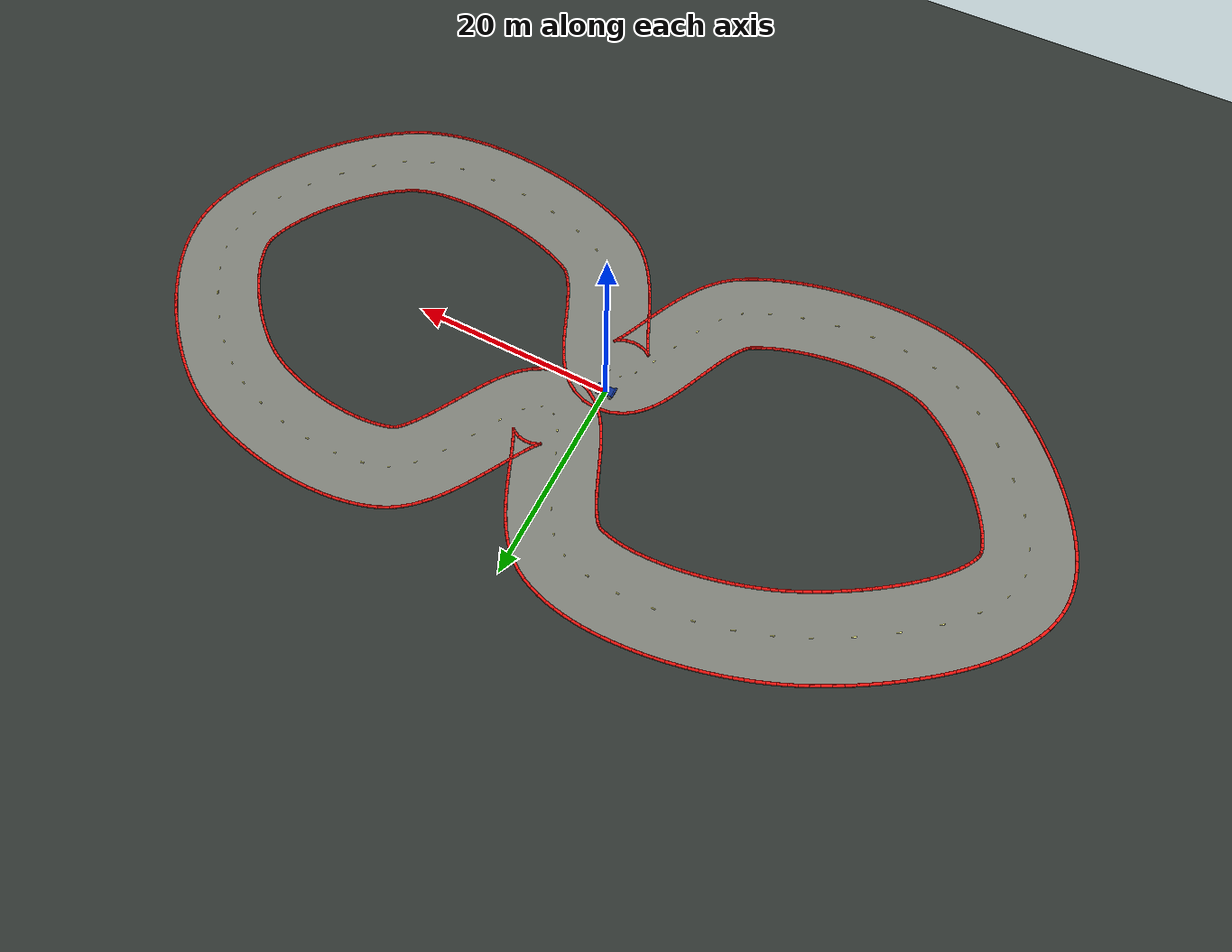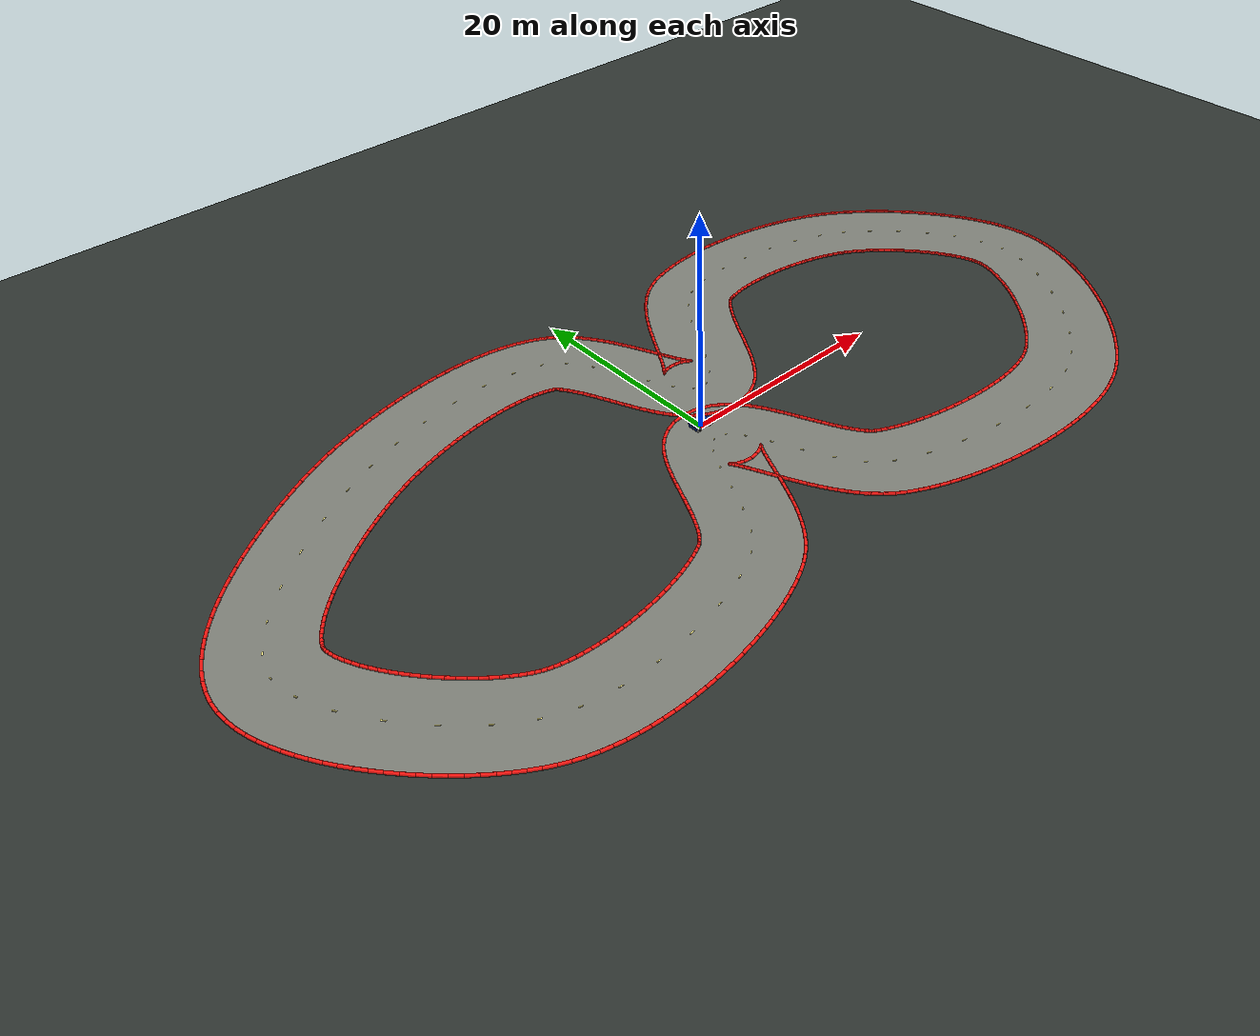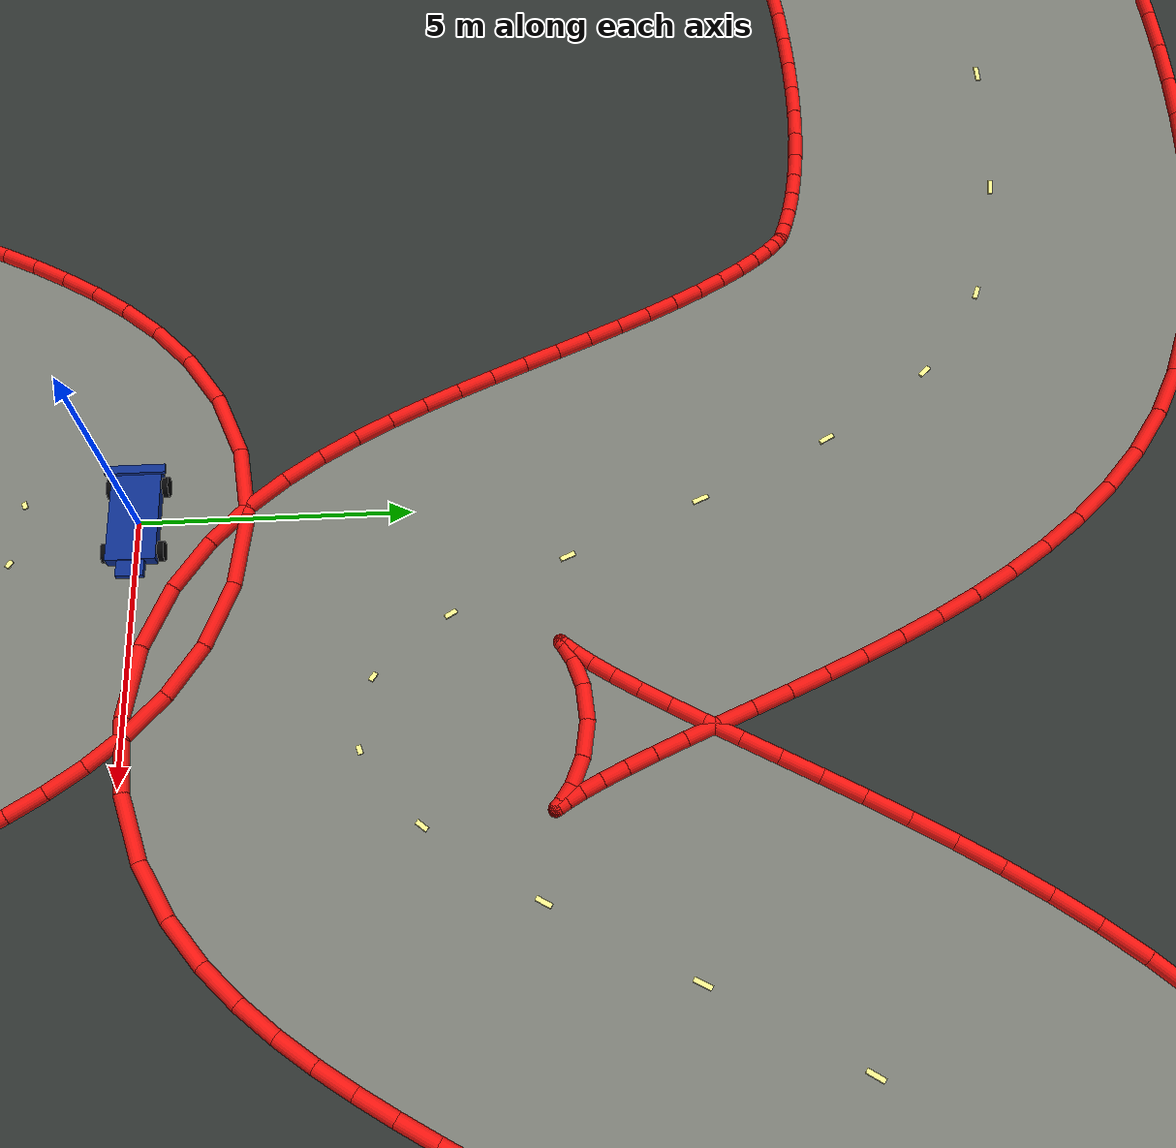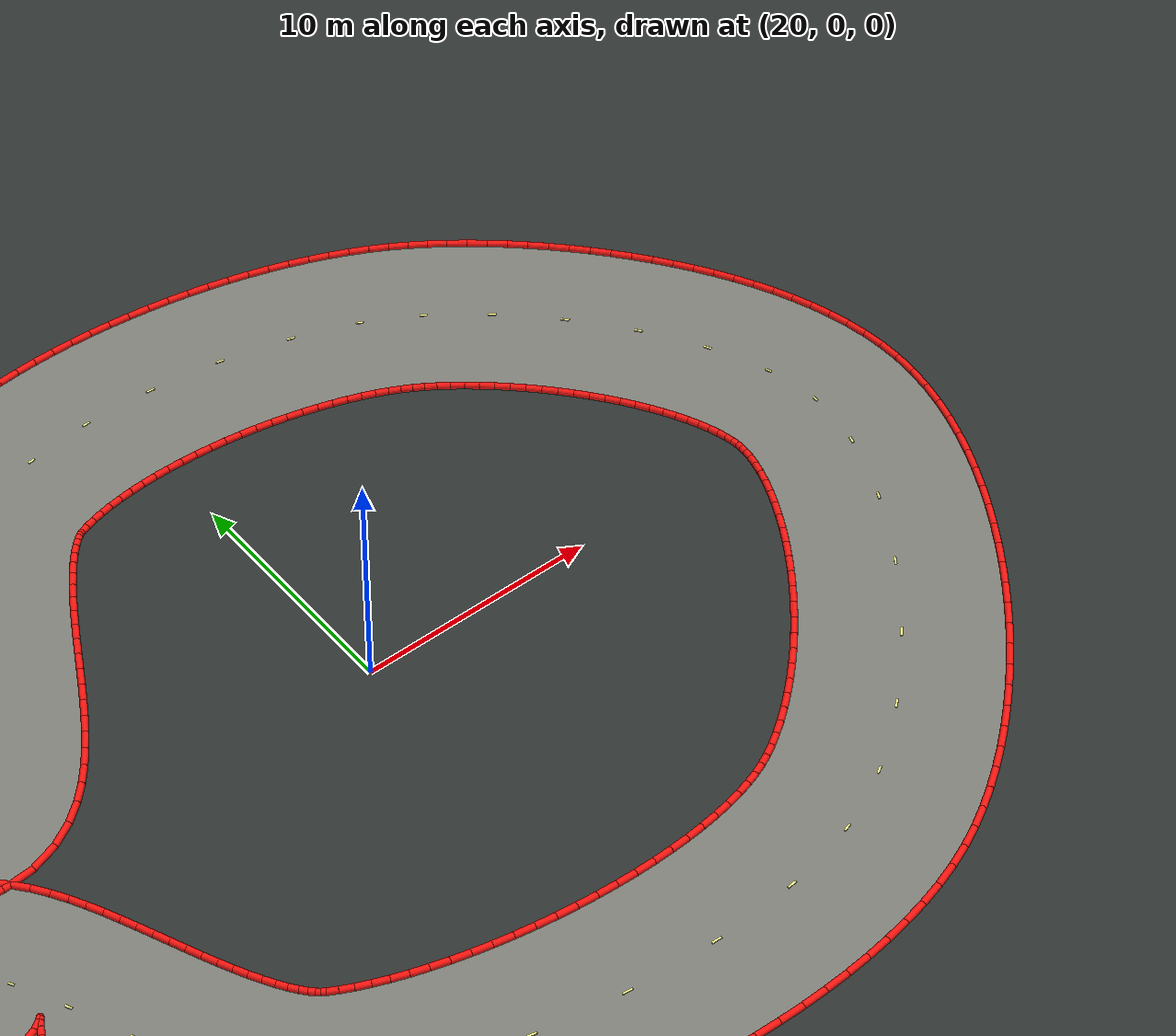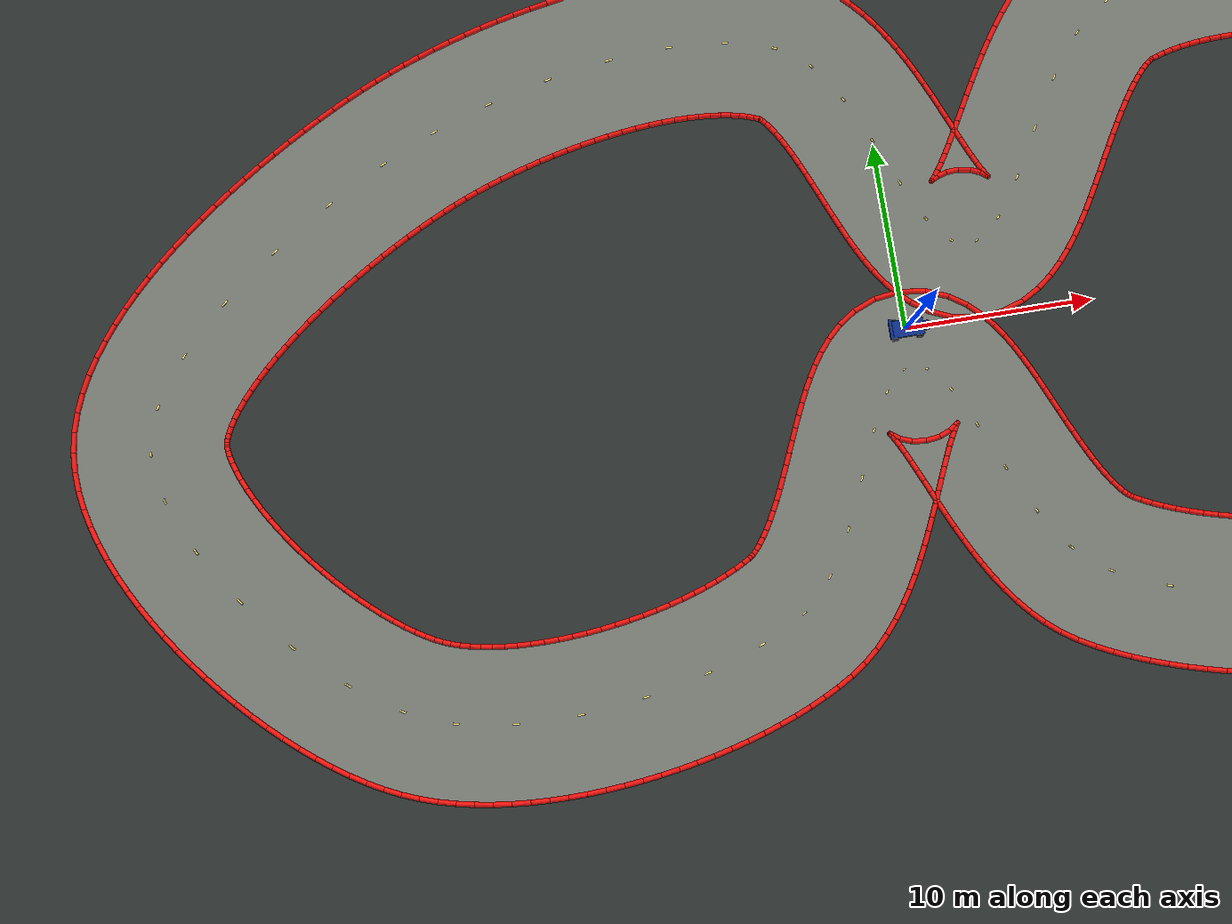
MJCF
<mujoco model="racesim_chicane_world">
  <compiler angle="degree" autolimits="true"/>
  <option timestep="0.02" gravity="0 0 -9.81"/>
  <visual>
    <global offwidth="1280" offheight="960"/>
    <headlight ambient="0.35 0.35 0.35" diffuse="0.8 0.8 0.8"/>
  </visual>

  <include file="car.xml"/>
  <include file="chicane_track.xml"/>

  <asset>
    <texture name="grid" type="2d" builtin="checker" width="512" height="512"
             rgb1="0.16 0.18 0.17" rgb2="0.20 0.22 0.21"/>
    <material name="ground" texture="grid" texrepeat="12 12" reflectance="0.05"/>
  </asset>

  <worldbody>
    <light name="sun" pos="0 0 30" dir="0 0 -1" diffuse="1.0 1.0 1.0" ambient="0.25 0.25 0.25"/>
    <geom name="ground" type="plane" size="90 90 0.1" material="ground"/>
    <camera name="topdown" pos="0 0 125" xyaxes="1 0 0 0 1 0" fovy="42"/>
    <camera name="follow" mode="trackcom" target="car" pos="-5 0 3" xyaxes="0 -1 0 0.5 0 0.866"/>
  </worldbody>
</mujoco>

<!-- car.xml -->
<mujoco model="simple_car">
  <default>
    <geom friction="1.2 0.02 0.001" density="600"/>
    <joint damping="0.1"/>
  </default>

  <asset>
    <material name="chassis_blue" rgba="0.05 0.18 0.55 1"/>
    <material name="wheel_dark" rgba="0.02 0.02 0.025 1"/>
  </asset>

  <worldbody>
    <body name="car" pos="0 0 0.28">
      <freejoint name="root"/>
      <geom name="chassis" type="box" size="0.9 0.45 0.12" material="chassis_blue"/>
      <geom name="nose" type="box" pos="0.75 0 0.02" size="0.45 0.25 0.06" material="chassis_blue"/>
      <geom name="rear_wing" type="box" pos="-0.85 0 0.22" size="0.08 0.55 0.04" material="chassis_blue"/>

      <body name="front_left_wheel" pos="0.65 0.48 -0.12">
        <joint name="front_left_spin" type="hinge" axis="0 1 0"/>
        <geom type="cylinder" size="0.18 0.08" euler="90 0 0" material="wheel_dark"/>
      </body>
      <body name="front_right_wheel" pos="0.65 -0.48 -0.12">
        <joint name="front_right_spin" type="hinge" axis="0 1 0"/>
        <geom type="cylinder" size="0.18 0.08" euler="90 0 0" material="wheel_dark"/>
      </body>
      <body name="rear_left_wheel" pos="-0.65 0.48 -0.12">
        <joint name="rear_left_spin" type="hinge" axis="0 1 0"/>
        <geom type="cylinder" size="0.18 0.08" euler="90 0 0" material="wheel_dark"/>
      </body>
      <body name="rear_right_wheel" pos="-0.65 -0.48 -0.12">
        <joint name="rear_right_spin" type="hinge" axis="0 1 0"/>
        <geom type="cylinder" size="0.18 0.08" euler="90 0 0" material="wheel_dark"/>
      </body>
    </body>
  </worldbody>
</mujoco>

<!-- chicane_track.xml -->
<mujoco model="chicane_track_visuals">
  <asset>
    <mesh name="track_surface_mesh" inertia="shell" vertex="38.00033 0.05129 0.02200 37.99257 0.27397 0.02200 37.96149 0.54448 0.02200 37.90211 0.85965 0.02200 37.81106 1.21477 0.02200 37.68643 1.60455 0.02200 37.52753 2.02365 0.02200 37.33459 2.46690 0.02200 37.10855 2.92944 0.02200 36.85085 3.40678 0.02200 36.56331 3.89474 0.02200 36.24797 4.38947 0.02200 35.90709 4.88738 0.02200 35.54306 5.38513 0.02200 35.15838 5.87955 0.02200 34.75561 6.36763 0.02200 34.33744 6.84651 0.02200 33.90661 7.31341 0.02200 33.46596 7.76563 0.02200 33.01842 8.20055 0.02200 32.56707 8.61559 0.02200 32.11514 9.00822 0.02200 31.66605 9.37592 0.02200 31.22350 9.71622 0.02200 30.79152 10.02669 0.02200 30.37457 10.30499 0.02200 29.98063 10.54716 0.02200 29.57226 10.77433 0.02200 29.12863 10.99669 0.02200 28.64663 11.21519 0.02200 28.13020 11.42719 0.02200 27.58325 11.63055 0.02200 27.00955 11.82346 0.02200 26.41283 12.00440 0.02200 25.79672 12.17210 0.02200 25.16479 12.32543 0.02200 24.52057 12.46344 0.02200 23.86755 12.58528 0.02200 23.20923 12.69024 0.02200 22.54908 12.77767 0.02200 21.89061 12.84705 0.02200 21.23736 12.89796 0.02200 20.59293 12.93006 0.02200 19.96100 12.94317 0.02200 19.34533 12.93724 0.02200 18.74980 12.91242 0.02200 18.17842 12.86907 0.02200 17.63534 12.80787 0.02200 17.12485 12.72986 0.02200 16.65137 12.63658 0.02200 16.21939 12.53020 0.02200 15.83332 12.41365 0.02200 15.56087 12.31711 0.02200 15.45473 12.26860 0.02200 15.34675 12.19662 0.02200 15.17004 12.05347 0.02200 14.93946 11.83333 0.02200 14.66920 11.53755 0.02200 14.37084 11.17164 0.02200 14.05313 10.74315 0.02200 13.72234 10.26038 0.02200 13.38278 9.73174 0.02200 13.03726 9.16539 0.02200 12.68744 8.56909 0.02200 12.33406 7.95011 0.02200 11.97709 7.31516 0.02200 11.61579 6.67040 0.02200 11.24863 6.02126 0.02200 10.87314 5.37239 0.02200 10.48559 4.72748 0.02200 10.08040 4.08901 0.02200 9.64913 3.45808 0.02200 9.17877 2.83435 0.02200 8.64898 2.21678 0.02200 8.02806 1.60652 0.02200 7.26941 1.01536 0.02200 6.31638 0.48405 0.02200 5.13512 0.10482 0.02200 3.79143 0.00544 0.02200 2.48261 0.24078 0.02200 1.36229 0.73352 0.02200 0.48016 1.35556 0.02200 -0.19960 2.01595 0.02200 -0.73560 2.67660 0.02200 -1.17600 3.32910 0.02200 -1.55348 3.97545 0.02200 -1.88904 4.61923 0.02200 -2.19621 5.26271 0.02200 -2.48392 5.90626 0.02200 -2.75829 6.54851 0.02200 -3.02362 7.18663 0.02200 -3.28301 7.81665 0.02200 -3.53865 8.43363 0.02200 -3.79197 9.03180 0.02200 -4.04369 9.60472 0.02200 -4.29371 10.14524 0.02200 -4.54097 10.64562 0.02200 -4.78313 11.09764 0.02200 -5.01616 11.49271 0.02200 -5.23383 11.82240 0.02200 -5.42714 12.07926 0.02200 -5.58404 12.25844 0.02200 -5.69008 12.36037 0.02200 -5.73129 12.39403 0.02200 -5.76749 12.41169 0.02200 -6.00428 12.50878 0.02200 -6.35547 12.62899 0.02200 -6.76476 12.74073 0.02200 -7.22810 12.83949 0.02200 -7.74085 12.92190 0.02200 -8.29818 12.98560 0.02200 -8.89528 13.02902 0.02200 -9.52743 13.05126 0.02200 -10.19013 13.05188 0.02200 -10.87904 13.03080 0.02200 -11.59000 12.98826 0.02200 -12.31903 12.92468 0.02200 -13.06229 12.84067 0.02200 -13.81605 12.73695 0.02200 -14.57671 12.61436 0.02200 -15.34071 12.47381 0.02200 -16.10458 12.31629 0.02200 -16.86489 12.14285 0.02200 -17.61823 11.95461 0.02200 -18.36120 11.75272 0.02200 -19.09039 11.53844 0.02200 -19.80238 11.31307 0.02200 -20.49368 11.07803 0.02200 -21.16075 10.83481 0.02200 -21.79993 10.58509 0.02200 -22.41054 10.32936 0.02200 -23.04560 10.04518 0.02200 -23.71330 9.72903 0.02200 -24.40641 9.38359 0.02200 -25.11933 9.01098 0.02200 -25.84675 8.61331 0.02200 -26.58355 8.19267 0.02200 -27.32475 7.75120 0.02200 -28.06545 7.29106 0.02200 -28.80081 6.81445 0.02200 -29.52599 6.32367 0.02200 -30.23618 5.82112 0.02200 -30.92654 5.30933 0.02200 -31.59220 4.79102 0.02200 -32.22826 4.26914 0.02200 -32.82978 3.74696 0.02200 -33.39179 3.22814 0.02200 -33.90932 2.71687 0.02200 -34.37749 2.21800 0.02200 -34.79158 1.73727 0.02200 -35.14732 1.28147 0.02200 -35.44121 0.85869 0.02200 -35.67121 0.47844 0.02200 -35.83762 0.15149 0.02200 -35.94441 -0.11090 0.02200 -36.00058 -0.29890 0.02200 -36.02232 -0.42198 0.02200 -36.02610 -0.54693 0.02200 -36.01078 -0.76316 0.02200 -35.96195 -1.06624 0.02200 -35.87043 -1.44429 0.02200 -35.73157 -1.88500 0.02200 -35.54391 -2.37686 0.02200 -35.30806 -2.90959 0.02200 -35.02592 -3.47415 0.02200 -34.70021 -4.06256 0.02200 -34.33413 -4.66771 0.02200 -33.93120 -5.28318 0.02200 -33.49513 -5.90311 0.02200 -33.02977 -6.52202 0.02200 -32.53910 -7.13476 0.02200 -32.02718 -7.73641 0.02200 -31.49822 -8.32222 0.02200 -30.95656 -8.88758 0.02200 -30.40675 -9.42796 0.02200 -29.85357 -9.93890 0.02200 -29.30214 -10.41599 0.02200 -28.75802 -10.85488 0.02200 -28.22738 -11.25128 0.02200 -27.71716 -11.60106 0.02200 -27.23540 -11.90036 0.02200 -26.79152 -12.14587 0.02200 -26.39480 -12.33621 0.02200 -25.99966 -12.49365 0.02200 -25.55373 -12.63940 0.02200 -25.05425 -12.77212 0.02200 -24.50634 -12.88839 0.02200 -23.91534 -12.98573 0.02200 -23.28656 -13.06244 0.02200 -22.62521 -13.11744 0.02200 -21.93636 -13.15011 0.02200 -21.22492 -13.16023 0.02200 -20.49565 -13.14783 0.02200 -19.75318 -13.11317 0.02200 -19.00203 -13.05672 0.02200 -18.24665 -12.97905 0.02200 -17.49140 -12.88091 0.02200 -16.74063 -12.76313 0.02200 -15.99867 -12.62666 0.02200 -15.26987 -12.47260 0.02200 -14.55860 -12.30215 0.02200 -13.86932 -12.11667 0.02200 -13.20657 -11.91773 0.02200 -12.57505 -11.70715 0.02200 -11.97962 -11.48706 0.02200 -11.42535 -11.26004 0.02200 -10.91756 -11.02927 0.02200 -10.46183 -10.79875 0.02200 -10.11800 -10.60676 0.02200 -9.97986 -10.51476 0.02200 -9.85173 -10.40312 0.02200 -9.67810 -10.22301 0.02200 -9.47049 -9.97263 0.02200 -9.23933 -9.65498 0.02200 -8.99291 -9.27581 0.02200 -8.73732 -8.84220 0.02200 -8.47681 -8.36165 0.02200 -8.21408 -7.84165 0.02200 -7.95070 -7.28939 0.02200 -7.68729 -6.71164 0.02200 -7.42376 -6.11470 0.02200 -7.15935 -5.50429 0.02200 -6.89270 -4.88551 0.02200 -6.62176 -4.26272 0.02200 -6.34363 -3.63936 0.02200 -6.05422 -3.01771 0.02200 -5.74764 -2.39858 0.02200 -5.41510 -1.78089 0.02200 -5.04302 -1.16141 0.02200 -4.60973 -0.53510 0.02200 -4.08043 0.10214 0.02200 -3.40177 0.74394 0.02200 -2.50586 1.35060 0.02200 -1.34978 1.81875 0.02200 -0.00045 2.00000 0.02200 1.34955 1.81883 0.02200 2.50760 1.34932 0.02200 3.40515 0.73961 0.02200 4.08361 0.09461 0.02200 4.61103 -0.54494 0.02200 5.04132 -1.17244 0.02200 5.40978 -1.79210 0.02200 5.73836 -2.40915 0.02200 6.04085 -3.02702 0.02200 6.32617 -3.64693 0.02200 6.60031 -4.26816 0.02200 6.86746 -4.88852 0.02200 7.13057 -5.50464 0.02200 7.39176 -6.11219 0.02200 7.65244 -6.70615 0.02200 7.91343 -7.28081 0.02200 8.17485 -7.82995 0.02200 8.43610 -8.34687 0.02200 8.69568 -8.82449 0.02200 8.95090 -9.25549 0.02200 9.19762 -9.63261 0.02200 9.42991 -9.94914 0.02200 9.63985 -10.19980 0.02200 9.81770 -10.38218 0.02200 9.95306 -10.49856 0.02200 10.09842 -10.59462 0.02200 10.47756 -10.80349 0.02200 10.97481 -11.04921 0.02200 11.53383 -11.29571 0.02200 12.14785 -11.53825 0.02200 12.81048 -11.77319 0.02200 13.51569 -11.99764 0.02200 14.25774 -12.20925 0.02200 15.03112 -12.40604 0.02200 15.83051 -12.58633 0.02200 16.65073 -12.74868 0.02200 17.48667 -12.89180 0.02200 18.33332 -13.01454 0.02200 19.18565 -13.11590 0.02200 20.03866 -13.19499 0.02200 20.88731 -13.25101 0.02200 21.72648 -13.28333 0.02200 22.55095 -13.29145 0.02200 23.35541 -13.27506 0.02200 24.13434 -13.23407 0.02200 24.88207 -13.16871 0.02200 25.59270 -13.07959 0.02200 26.26010 -12.96785 0.02200 26.87794 -12.83534 0.02200 27.43978 -12.68481 0.02200 27.93924 -12.52022 0.02200 28.38181 -12.34193 0.02200 28.79168 -12.14348 0.02200 29.24137 -11.89322 0.02200 29.72011 -11.59385 0.02200 30.22062 -11.24788 0.02200 30.73648 -10.85840 0.02200 31.26205 -10.42884 0.02200 31.79223 -9.96282 0.02200 32.32241 -9.46410 0.02200 32.84835 -8.93653 0.02200 33.36608 -8.38400 0.02200 33.87187 -7.81051 0.02200 34.36217 -7.22010 0.02200 34.83356 -6.61690 0.02200 35.28276 -6.00519 0.02200 35.70658 -5.38938 0.02200 36.10195 -4.77407 0.02200 36.46590 -4.16413 0.02200 36.79560 -3.56477 0.02200 37.08842 -2.98160 0.02200 37.34200 -2.42075 0.02200 37.55439 -1.88903 0.02200 37.72430 -1.39399 0.02200 37.85142 -0.94409 0.02200 37.93696 -0.54865 0.02200 37.98435 -0.21764 0.02200 45.99967 -0.05129 0.02200 45.97190 0.84862 0.02200 45.87356 1.72732 0.02200 45.71402 2.58420 0.02200 45.50106 3.42020 0.02200 45.24098 4.23680 0.02200 44.93889 5.03557 0.02200 44.59894 5.81790 0.02200 44.22459 6.58484 0.02200 43.81880 7.33713 0.02200 43.38417 8.07515 0.02200 42.92303 8.79895 0.02200 42.43754 9.50835 0.02200 41.92970 10.20290 0.02200 41.40142 10.88199 0.02200 40.85451 11.54484 0.02200 40.29072 12.19053 0.02200 39.71168 12.81805 0.02200 39.11898 13.42632 0.02200 38.51405 14.01416 0.02200 37.89824 14.58038 0.02200 37.27271 15.12373 0.02200 36.63843 15.64293 0.02200 35.99611 16.13667 0.02200 35.34613 16.60359 0.02200 34.68841 17.04226 0.02200 34.01937 17.45284 0.02200 33.31122 17.84682 0.02200 32.57500 18.21629 0.02200 31.81904 18.55929 0.02200 31.04464 18.87743 0.02200 30.25315 19.17188 0.02200 29.44600 19.44341 0.02200 28.62471 19.69255 0.02200 27.79090 19.91957 0.02200 26.94622 20.12457 0.02200 26.09239 20.30751 0.02200 25.23113 20.46822 0.02200 24.36421 20.60642 0.02200 23.49338 20.72174 0.02200 22.62037 20.81370 0.02200 21.74686 20.88171 0.02200 20.87451 20.92510 0.02200 20.00487 20.94305 0.02200 19.13941 20.93459 0.02200 18.27949 20.89858 0.02200 17.42633 20.83364 0.02200 16.58103 20.73809 0.02200 15.74452 20.60988 0.02200 14.91763 20.44645 0.02200 14.10110 20.24465 0.02200 13.29575 20.00053 0.02200 12.43913 19.68289 0.02200 11.54359 19.24735 0.02200 10.68149 18.69550 0.02200 9.91809 18.08812 0.02200 9.23691 17.44411 0.02200 8.62214 16.77521 0.02200 8.06056 16.08899 0.02200 7.54179 15.39099 0.02200 7.05795 14.68598 0.02200 6.60311 13.97862 0.02200 6.17282 13.27386 0.02200 5.76381 12.57701 0.02200 5.37370 11.89388 0.02200 5.00089 11.23084 0.02200 4.64451 10.59483 0.02200 4.30447 9.99348 0.02200 3.98160 9.43523 0.02200 3.67800 8.92948 0.02200 3.39764 8.48682 0.02200 3.14733 8.11925 0.02200 2.93845 7.84017 0.02200 2.78973 7.66372 0.02200 2.73122 7.60181 0.02200 2.80790 7.65576 0.02200 3.07482 7.79789 0.02200 3.56419 7.94906 0.02200 4.20857 7.99456 0.02200 4.85761 7.88011 0.02200 5.34840 7.66972 0.02200 5.62791 7.47933 0.02200 5.72864 7.38773 0.02200 5.70584 7.42084 0.02200 5.60435 7.57491 0.02200 5.45351 7.83579 0.02200 5.27098 8.18773 0.02200 5.06694 8.61631 0.02200 4.84700 9.10900 0.02200 4.61393 9.65500 0.02200 4.36870 10.24498 0.02200 4.11107 10.87076 0.02200 3.83988 11.52511 0.02200 3.55324 12.20164 0.02200 3.24853 12.89464 0.02200 2.92230 13.59909 0.02200 2.57016 14.31057 0.02200 2.18643 15.02515 0.02200 1.76374 15.73924 0.02200 1.29253 16.44913 0.02200 0.76046 17.15011 0.02200 0.15214 17.83484 0.02200 -0.55023 18.49078 0.02200 -1.36394 19.09674 0.02200 -2.23251 19.58831 0.02200 -3.13398 19.97613 0.02200 -3.99623 20.27320 0.02200 -4.87019 20.51316 0.02200 -5.75450 20.70260 0.02200 -6.64839 20.84696 0.02200 -7.55131 20.95066 0.02200 -8.46268 21.01732 0.02200 -9.38180 21.04994 0.02200 -10.30778 21.05101 0.02200 -11.23958 21.02268 0.02200 -12.17594 20.96677 0.02200 -13.11546 20.88494 0.02200 -14.05657 20.77864 0.02200 -14.99760 20.64922 0.02200 -15.93677 20.49790 0.02200 -16.87223 20.32585 0.02200 -17.80205 20.13413 0.02200 -18.72428 19.92377 0.02200 -19.63692 19.69572 0.02200 -20.53797 19.45088 0.02200 -21.42545 19.19008 0.02200 -22.29738 18.91406 0.02200 -23.15185 18.62350 0.02200 -23.98702 18.31894 0.02200 -24.80112 18.00080 0.02200 -25.58946 17.67064 0.02200 -26.39091 17.31215 0.02200 -27.20926 16.92475 0.02200 -28.04352 16.50900 0.02200 -28.89102 16.06608 0.02200 -29.74882 15.59713 0.02200 -30.61378 15.10333 0.02200 -31.48264 14.58581 0.02200 -32.35205 14.04569 0.02200 -33.21859 13.48402 0.02200 -34.07885 12.90178 0.02200 -34.92939 12.29984 0.02200 -35.76680 11.67894 0.02200 -36.58769 11.03963 0.02200 -37.38872 10.38222 0.02200 -38.16657 9.70672 0.02200 -38.91796 9.01273 0.02200 -39.63960 8.29933 0.02200 -40.32814 7.56494 0.02200 -40.98003 6.80710 0.02200 -41.59129 6.02227 0.02200 -42.15717 5.20564 0.02200 -42.67146 4.35098 0.02200 -43.12561 3.45077 0.02200 -43.50740 2.49702 0.02200 -43.79957 1.48317 0.02200 -43.97768 0.42198 0.02200 -44.02572 -0.62462 0.02200 -43.96255 -1.64026 0.02200 -43.80913 -2.62246 0.02200 -43.58116 -3.57610 0.02200 -43.28983 -4.50657 0.02200 -42.94316 -5.41843 0.02200 -42.54706 -6.31500 0.02200 -42.10618 -7.19838 0.02200 -41.62434 -8.06960 0.02200 -41.10487 -8.92881 0.02200 -40.55081 -9.77549 0.02200 -39.96497 -10.60855 0.02200 -39.35005 -11.42652 0.02200 -38.70861 -12.22761 0.02200 -38.04313 -13.00977 0.02200 -37.35593 -13.77081 0.02200 -36.64922 -14.50840 0.02200 -35.92499 -15.22011 0.02200 -35.18500 -15.90345 0.02200 -34.43066 -16.55588 0.02200 -33.66296 -17.17481 0.02200 -32.88227 -17.75758 0.02200 -32.08818 -18.30137 0.02200 -31.27921 -18.80308 0.02200 -30.45246 -19.25907 0.02200 -29.60520 -19.66379 0.02200 -28.72939 -20.01353 0.02200 -27.82996 -20.30874 0.02200 -26.91630 -20.55240 0.02200 -25.98991 -20.74963 0.02200 -25.05208 -20.90455 0.02200 -24.10412 -21.02055 0.02200 -23.14746 -21.10037 0.02200 -22.18364 -21.14629 0.02200 -21.21439 -21.16022 0.02200 -20.24157 -21.14379 0.02200 -19.26717 -21.09840 0.02200 -18.29330 -21.02526 0.02200 -17.32215 -20.92545 0.02200 -16.35596 -20.79992 0.02200 -15.39702 -20.64949 0.02200 -14.44762 -20.47486 0.02200 -13.51006 -20.27664 0.02200 -12.58656 -20.05528 0.02200 -11.67931 -19.81108 0.02200 -10.79038 -19.54414 0.02200 -9.92171 -19.25432 0.02200 -9.07506 -18.94116 0.02200 -8.25199 -18.60373 0.02200 -7.45380 -18.24054 0.02200 -6.68154 -17.84924 0.02200 -5.88200 -17.39324 0.02200 -5.11312 -16.86416 0.02200 -4.37996 -16.23919 0.02200 -3.73524 -15.57861 0.02200 -3.16461 -14.89561 0.02200 -2.65487 -14.19863 0.02200 -2.19492 -13.49332 0.02200 -1.77586 -12.78403 0.02200 -1.39066 -12.07469 0.02200 -1.03381 -11.36921 0.02200 -0.70094 -10.67184 0.02200 -0.38862 -9.98722 0.02200 -0.09416 -9.32047 0.02200 0.18449 -8.67729 0.02200 0.44877 -8.06399 0.02200 0.69943 -7.48765 0.02200 0.93636 -6.95624 0.02200 1.15828 -6.47889 0.02200 1.36210 -6.06623 0.02200 1.54182 -5.73073 0.02200 1.68667 -5.48708 0.02200 1.77778 -5.35171 0.02200 1.78314 -5.34015 0.02200 1.65220 -5.45746 0.02200 1.31989 -5.67533 0.02200 0.74606 -5.90184 0.02200 0.00045 -6.00000 0.02200 -0.74659 -5.90167 0.02200 -1.32455 -5.67312 0.02200 -1.66191 -5.45110 0.02200 -1.79707 -5.32919 0.02200 -1.79510 -5.33676 0.02200 -1.70696 -5.46903 0.02200 -1.56492 -5.71046 0.02200 -1.38799 -6.04442 0.02200 -1.18695 -6.45615 0.02200 -0.96775 -6.93307 0.02200 -0.73340 -7.46451 0.02200 -0.48508 -8.04133 0.02200 -0.22279 -8.65552 0.02200 0.05434 -9.30005 0.02200 0.34789 -9.96859 0.02200 0.66004 -10.65547 0.02200 0.99362 -11.35556 0.02200 1.35222 -12.06420 0.02200 1.74034 -12.77711 0.02200 2.16364 -13.49025 0.02200 2.62925 -14.19950 0.02200 3.14608 -14.90023 0.02200 3.72503 -15.58635 0.02200 4.37882 -16.24891 0.02200 5.12084 -16.87427 0.02200 5.90158 -17.40538 0.02200 6.75250 -17.88332 0.02200 7.58512 -18.29559 0.02200 8.44793 -18.67658 0.02200 9.33985 -19.02925 0.02200 10.25939 -19.35554 0.02200 11.20475 -19.65659 0.02200 12.17380 -19.93305 0.02200 13.16421 -20.18515 0.02200 14.17345 -20.41283 0.02200 15.19884 -20.61583 0.02200 16.23763 -20.79369 0.02200 17.28699 -20.94582 0.02200 18.34408 -21.07152 0.02200 19.40605 -21.16993 0.02200 20.47011 -21.24012 0.02200 21.53350 -21.28100 0.02200 22.59359 -21.29134 0.02200 23.64785 -21.26971 0.02200 24.69393 -21.21448 0.02200 25.72965 -21.12368 0.02200 26.75307 -20.99499 0.02200 27.76246 -20.82552 0.02200 28.75629 -20.61170 0.02200 29.73315 -20.34904 0.02200 30.69156 -20.03186 0.02200 31.61819 -19.65807 0.02200 32.47479 -19.24522 0.02200 33.30485 -18.78438 0.02200 34.11407 -18.27914 0.02200 34.90464 -17.73324 0.02200 35.67785 -17.14990 0.02200 36.43428 -16.53196 0.02200 37.17390 -15.88208 0.02200 37.89624 -15.20278 0.02200 38.60046 -14.49650 0.02200 39.28540 -13.76560 0.02200 39.94973 -13.01241 0.02200 40.59188 -12.23913 0.02200 41.21018 -11.44792 0.02200 41.80282 -10.64079 0.02200 42.36789 -9.81961 0.02200 42.90336 -8.98605 0.02200 43.40711 -8.14152 0.02200 43.87686 -7.28710 0.02200 44.31016 -6.42346 0.02200 44.70428 -5.55074 0.02200 45.05605 -4.66843 0.02200 45.36168 -3.77524 0.02200 45.61638 -2.86900 0.02200 45.81386 -1.94667 0.02200 45.94556 -1.00455 0.02200" face="0 313 1 0 312 313 1 314 2 1 313 314 2 315 3 2 314 315 3 316 4 3 315 316 4 317 5 4 316 317 5 318 6 5 317 318 6 319 7 6 318 319 7 320 8 7 319 320 8 321 9 8 320 321 9 322 10 9 321 322 10 323 11 10 322 323 11 324 12 11 323 324 12 325 13 12 324 325 13 326 14 13 325 326 14 327 15 14 326 327 15 328 16 15 327 328 16 329 17 16 328 329 17 330 18 17 329 330 18 331 19 18 330 331 19 332 20 19 331 332 20 333 21 20 332 333 21 334 22 21 333 334 22 335 23 22 334 335 23 336 24 23 335 336 24 337 25 24 336 337 25 338 26 25 337 338 26 339 27 26 338 339 27 340 28 27 339 340 28 341 29 28 340 341 29 342 30 29 341 342 30 343 31 30 342 343 31 344 32 31 343 344 32 345 33 32 344 345 33 346 34 33 345 346 34 347 35 34 346 347 35 348 36 35 347 348 36 349 37 36 348 349 37 350 38 37 349 350 38 351 39 38 350 351 39 352 40 39 351 352 40 353 41 40 352 353 41 354 42 41 353 354 42 355 43 42 354 355 43 356 44 43 355 356 44 357 45 44 356 357 45 358 46 45 357 358 46 359 47 46 358 359 47 360 48 47 359 360 48 361 49 48 360 361 49 362 50 49 361 362 50 363 51 50 362 363 51 364 52 51 363 364 52 365 53 52 364 365 53 366 54 53 365 366 54 367 55 54 366 367 55 368 56 55 367 368 56 369 57 56 368 369 57 370 58 57 369 370 58 371 59 58 370 371 59 372 60 59 371 372 60 373 61 60 372 373 61 374 62 61 373 374 62 375 63 62 374 375 63 376 64 63 375 376 64 377 65 64 376 377 65 378 66 65 377 378 66 379 67 66 378 379 67 380 68 67 379 380 68 381 69 68 380 381 69 382 70 69 381 382 70 383 71 70 382 383 71 384 72 71 383 384 72 385 73 72 384 385 73 386 74 73 385 386 74 387 75 74 386 387 75 388 76 75 387 388 76 389 77 76 388 389 77 390 78 77 389 390 78 391 79 78 390 391 79 392 80 79 391 392 80 393 81 80 392 393 81 394 82 81 393 394 82 395 83 82 394 395 83 396 84 83 395 396 84 397 85 84 396 397 85 398 86 85 397 398 86 399 87 86 398 399 87 400 88 87 399 400 88 401 89 88 400 401 89 402 90 89 401 402 90 403 91 90 402 403 91 404 92 91 403 404 92 405 93 92 404 405 93 406 94 93 405 406 94 407 95 94 406 407 95 408 96 95 407 408 96 409 97 96 408 409 97 410 98 97 409 410 98 411 99 98 410 411 99 412 100 99 411 412 100 413 101 100 412 413 101 414 102 101 413 414 102 415 103 102 414 415 103 416 104 103 415 416 104 417 105 104 416 417 105 418 106 105 417 418 106 419 107 106 418 419 107 420 108 107 419 420 108 421 109 108 420 421 109 422 110 109 421 422 110 423 111 110 422 423 111 424 112 111 423 424 112 425 113 112 424 425 113 426 114 113 425 426 114 427 115 114 426 427 115 428 116 115 427 428 116 429 117 116 428 429 117 430 118 117 429 430 118 431 119 118 430 431 119 432 120 119 431 432 120 433 121 120 432 433 121 434 122 121 433 434 122 435 123 122 434 435 123 436 124 123 435 436 124 437 125 124 436 437 125 438 126 125 437 438 126 439 127 126 438 439 127 440 128 127 439 440 128 441 129 128 440 441 129 442 130 129 441 442 130 443 131 130 442 443 131 444 132 131 443 444 132 445 133 132 444 445 133 446 134 133 445 446 134 447 135 134 446 447 135 448 136 135 447 448 136 449 137 136 448 449 137 450 138 137 449 450 138 451 139 138 450 451 139 452 140 139 451 452 140 453 141 140 452 453 141 454 142 141 453 454 142 455 143 142 454 455 143 456 144 143 455 456 144 457 145 144 456 457 145 458 146 145 457 458 146 459 147 146 458 459 147 460 148 147 459 460 148 461 149 148 460 461 149 462 150 149 461 462 150 463 151 150 462 463 151 464 152 151 463 464 152 465 153 152 464 465 153 466 154 153 465 466 154 467 155 154 466 467 155 468 156 155 467 468 156 469 157 156 468 469 157 470 158 157 469 470 158 471 159 158 470 471 159 472 160 159 471 472 160 473 161 160 472 473 161 474 162 161 473 474 162 475 163 162 474 475 163 476 164 163 475 476 164 477 165 164 476 477 165 478 166 165 477 478 166 479 167 166 478 479 167 480 168 167 479 480 168 481 169 168 480 481 169 482 170 169 481 482 170 483 171 170 482 483 171 484 172 171 483 484 172 485 173 172 484 485 173 486 174 173 485 486 174 487 175 174 486 487 175 488 176 175 487 488 176 489 177 176 488 489 177 490 178 177 489 490 178 491 179 178 490 491 179 492 180 179 491 492 180 493 181 180 492 493 181 494 182 181 493 494 182 495 183 182 494 495 183 496 184 183 495 496 184 497 185 184 496 497 185 498 186 185 497 498 186 499 187 186 498 499 187 500 188 187 499 500 188 501 189 188 500 501 189 502 190 189 501 502 190 503 191 190 502 503 191 504 192 191 503 504 192 505 193 192 504 505 193 506 194 193 505 506 194 507 195 194 506 507 195 508 196 195 507 508 196 509 197 196 508 509 197 510 198 197 509 510 198 511 199 198 510 511 199 512 200 199 511 512 200 513 201 200 512 513 201 514 202 201 513 514 202 515 203 202 514 515 203 516 204 203 515 516 204 517 205 204 516 517 205 518 206 205 517 518 206 519 207 206 518 519 207 520 208 207 519 520 208 521 209 208 520 521 209 522 210 209 521 522 210 523 211 210 522 523 211 524 212 211 523 524 212 525 213 212 524 525 213 526 214 213 525 526 214 527 215 214 526 527 215 528 216 215 527 528 216 529 217 216 528 529 217 530 218 217 529 530 218 531 219 218 530 531 219 532 220 219 531 532 220 533 221 220 532 533 221 534 222 221 533 534 222 535 223 222 534 535 223 536 224 223 535 536 224 537 225 224 536 537 225 538 226 225 537 538 226 539 227 226 538 539 227 540 228 227 539 540 228 541 229 228 540 541 229 542 230 229 541 542 230 543 231 230 542 543 231 544 232 231 543 544 232 545 233 232 544 545 233 546 234 233 545 546 234 547 235 234 546 547 235 548 236 235 547 548 236 549 237 236 548 549 237 550 238 237 549 550 238 551 239 238 550 551 239 552 240 239 551 552 240 553 241 240 552 553 241 554 242 241 553 554 242 555 243 242 554 555 243 556 244 243 555 556 244 557 245 244 556 557 245 558 246 245 557 558 246 559 247 246 558 559 247 560 248 247 559 560 248 561 249 248 560 561 249 562 250 249 561 562 250 563 251 250 562 563 251 564 252 251 563 564 252 565 253 252 564 565 253 566 254 253 565 566 254 567 255 254 566 567 255 568 256 255 567 568 256 569 257 256 568 569 257 570 258 257 569 570 258 571 259 258 570 571 259 572 260 259 571 572 260 573 261 260 572 573 261 574 262 261 573 574 262 575 263 262 574 575 263 576 264 263 575 576 264 577 265 264 576 577 265 578 266 265 577 578 266 579 267 266 578 579 267 580 268 267 579 580 268 581 269 268 580 581 269 582 270 269 581 582 270 583 271 270 582 583 271 584 272 271 583 584 272 585 273 272 584 585 273 586 274 273 585 586 274 587 275 274 586 587 275 588 276 275 587 588 276 589 277 276 588 589 277 590 278 277 589 590 278 591 279 278 590 591 279 592 280 279 591 592 280 593 281 280 592 593 281 594 282 281 593 594 282 595 283 282 594 595 283 596 284 283 595 596 284 597 285 284 596 597 285 598 286 285 597 598 286 599 287 286 598 599 287 600 288 287 599 600 288 601 289 288 600 601 289 602 290 289 601 602 290 603 291 290 602 603 291 604 292 291 603 604 292 605 293 292 604 605 293 606 294 293 605 606 294 607 295 294 606 607 295 608 296 295 607 608 296 609 297 296 608 609 297 610 298 297 609 610 298 611 299 298 610 611 299 612 300 299 611 612 300 613 301 300 612 613 301 614 302 301 613 614 302 615 303 302 614 615 303 616 304 303 615 616 304 617 305 304 616 617 305 618 306 305 617 618 306 619 307 306 618 619 307 620 308 307 619 620 308 621 309 308 620 621 309 622 310 309 621 622 310 623 311 310 622 623 311 312 0 311 623 312"/>
    <material name="track_asphalt" rgba="0.48 0.49 0.46 1" emission="0.08"/>
    <material name="track_boundary" rgba="0.95 0.08 0.06 1" emission="0.05"/>
    <material name="track_centerline" rgba="1.0 0.95 0.55 1" emission="0.15"/>
  </asset>
  <worldbody>
    <geom name="track_surface" type="mesh" mesh="track_surface_mesh" material="track_asphalt" contype="0" conaffinity="0"/>
    <geom name="track_left_boundary_000" type="capsule" fromto="38.00033 0.05129 0.09 37.99257 0.27397 0.09" size="0.14" material="track_boundary" contype="0" conaffinity="0"/>
    <geom name="track_left_boundary_001" type="capsule" fromto="37.99257 0.27397 0.09 37.96149 0.54448 0.09" size="0.14" material="track_boundary" contype="0" conaffinity="0"/>
    <geom name="track_left_boundary_002" type="capsule" fromto="37.96149 0.54448 0.09 37.90211 0.85965 0.09" size="0.14" material="track_boundary" contype="0" conaffinity="0"/>
    <geom name="track_left_boundary_003" type="capsule" fromto="37.90211 0.85965 0.09 37.81106 1.21477 0.09" size="0.14" material="track_boundary" contype="0" conaffinity="0"/>
    <geom name="track_left_boundary_004" type="capsule" fromto="37.81106 1.21477 0.09 37.68643 1.60455 0.09" size="0.14" material="track_boundary" contype="0" conaffinity="0"/>
    <geom name="track_left_boundary_005" type="capsule" fromto="37.68643 1.60455 0.09 37.52753 2.02365 0.09" size="0.14" material="track_boundary" contype="0" conaffinity="0"/>
    <geom name="track_left_boundary_006" type="capsule" fromto="37.52753 2.02365 0.09 37.33459 2.46690 0.09" size="0.14" material="track_boundary" contype="0" conaffinity="0"/>
    <geom name="track_left_boundary_007" type="capsule" fromto="37.33459 2.46690 0.09 37.10855 2.92944 0.09" size="0.14" material="track_boundary" contype="0" conaffinity="0"/>
    <geom name="track_left_boundary_008" type="capsule" fromto="37.10855 2.92944 0.09 36.85085 3.40678 0.09" size="0.14" material="track_boundary" contype="0" conaffinity="0"/>
    <geom name="track_left_boundary_009" type="capsule" fromto="36.85085 3.40678 0.09 36.56331 3.89474 0.09" size="0.14" material="track_boundary" contype="0" conaffinity="0"/>
    <geom name="track_left_boundary_010" type="capsule" fromto="36.56331 3.89474 0.09 36.24797 4.38947 0.09" size="0.14" material="track_boundary" contype="0" conaffinity="0"/>
    <geom name="track_left_boundary_011" type="capsule" fromto="36.24797 4.38947 0.09 35.90709 4.88738 0.09" size="0.14" material="track_boundary" contype="0" conaffinity="0"/>
    <geom name="track_left_boundary_012" type="capsule" fromto="35.90709 4.88738 0.09 35.54306 5.38513 0.09" size="0.14" material="track_boundary" contype="0" conaffinity="0"/>
    <geom name="track_left_boundary_013" type="capsule" fromto="35.54306 5.38513 0.09 35.15838 5.87955 0.09" size="0.14" material="track_boundary" contype="0" conaffinity="0"/>
    <geom name="track_left_boundary_014" type="capsule" fromto="35.15838 5.87955 0.09 34.75561 6.36763 0.09" size="0.14" material="track_boundary" contype="0" conaffinity="0"/>
    <geom name="track_left_boundary_015" type="capsule" fromto="34.75561 6.36763 0.09 34.33744 6.84651 0.09" size="0.14" material="track_boundary" contype="0" conaffinity="0"/>
    <geom name="track_left_boundary_016" type="capsule" fromto="34.33744 6.84651 0.09 33.90661 7.31341 0.09" size="0.14" material="track_boundary" contype="0" conaffinity="0"/>
    <geom name="track_left_boundary_017" type="capsule" fromto="33.90661 7.31341 0.09 33.46596 7.76563 0.09" size="0.14" material="track_boundary" contype="0" conaffinity="0"/>
    <geom name="track_left_boundary_018" type="capsule" fromto="33.46596 7.76563 0.09 33.01842 8.20055 0.09" size="0.14" material="track_boundary" contype="0" conaffinity="0"/>
    <geom name="track_left_boundary_019" type="capsule" fromto="33.01842 8.20055 0.09 32.56707 8.61559 0.09" size="0.14" material="track_boundary" contype="0" conaffinity="0"/>
    <geom name="track_left_boundary_020" type="capsule" fromto="32.56707 8.61559 0.09 32.11514 9.00822 0.09" size="0.14" material="track_boundary" contype="0" conaffinity="0"/>
    <geom name="track_left_boundary_021" type="capsule" fromto="32.11514 9.00822 0.09 31.66605 9.37592 0.09" size="0.14" material="track_boundary" contype="0" conaffinity="0"/>
    <geom name="track_left_boundary_022" type="capsule" fromto="31.66605 9.37592 0.09 31.22350 9.71622 0.09" size="0.14" material="track_boundary" contype="0" conaffinity="0"/>
    <geom name="track_left_boundary_023" type="capsule" fromto="31.22350 9.71622 0.09 30.79152 10.02669 0.09" size="0.14" material="track_boundary" contype="0" conaffinity="0"/>
    <geom name="track_left_boundary_024" type="capsule" fromto="30.79152 10.02669 0.09 30.37457 10.30499 0.09" size="0.14" material="track_boundary" contype="0" conaffinity="0"/>
    <geom name="track_left_boundary_025" type="capsule" fromto="30.37457 10.30499 0.09 29.98063 10.54716 0.09" size="0.14" material="track_boundary" contype="0" conaffinity="0"/>
    <geom name="track_left_boundary_026" type="capsule" fromto="29.98063 10.54716 0.09 29.57226 10.77433 0.09" size="0.14" material="track_boundary" contype="0" conaffinity="0"/>
    <geom name="track_left_boundary_027" type="capsule" fromto="29.57226 10.77433 0.09 29.12863 10.99669 0.09" size="0.14" material="track_boundary" contype="0" conaffinity="0"/>
    <geom name="track_left_boundary_028" type="capsule" fromto="29.12863 10.99669 0.09 28.64663 11.21519 0.09" size="0.14" material="track_boundary" contype="0" conaffinity="0"/>
    <geom name="track_left_boundary_029" type="capsule" fromto="28.64663 11.21519 0.09 28.13020 11.42719 0.09" size="0.14" material="track_boundary" contype="0" conaffinity="0"/>
    <geom name="track_left_boundary_030" type="capsule" fromto="28.13020 11.42719 0.09 27.58325 11.63055 0.09" size="0.14" material="track_boundary" contype="0" conaffinity="0"/>
    <geom name="track_left_boundary_031" type="capsule" fromto="27.58325 11.63055 0.09 27.00955 11.82346 0.09" size="0.14" material="track_boundary" contype="0" conaffinity="0"/>
    <geom name="track_left_boundary_032" type="capsule" fromto="27.00955 11.82346 0.09 26.41283 12.00440 0.09" size="0.14" material="track_boundary" contype="0" conaffinity="0"/>
    <geom name="track_left_boundary_033" type="capsule" fromto="26.41283 12.00440 0.09 25.79672 12.17210 0.09" size="0.14" material="track_boundary" contype="0" conaffinity="0"/>
    <geom name="track_left_boundary_034" type="capsule" fromto="25.79672 12.17210 0.09 25.16479 12.32543 0.09" size="0.14" material="track_boundary" contype="0" conaffinity="0"/>
    <geom name="track_left_boundary_035" type="capsule" fromto="25.16479 12.32543 0.09 24.52057 12.46344 0.09" size="0.14" material="track_boundary" contype="0" conaffinity="0"/>
    <geom name="track_left_boundary_036" type="capsule" fromto="24.52057 12.46344 0.09 23.86755 12.58528 0.09" size="0.14" material="track_boundary" contype="0" conaffinity="0"/>
    <geom name="track_left_boundary_037" type="capsule" fromto="23.86755 12.58528 0.09 23.20923 12.69024 0.09" size="0.14" material="track_boundary" contype="0" conaffinity="0"/>
    <geom name="track_left_boundary_038" type="capsule" fromto="23.20923 12.69024 0.09 22.54908 12.77767 0.09" size="0.14" material="track_boundary" contype="0" conaffinity="0"/>
    <geom name="track_left_boundary_039" type="capsule" fromto="22.54908 12.77767 0.09 21.89061 12.84705 0.09" size="0.14" material="track_boundary" contype="0" conaffinity="0"/>
    <geom name="track_left_boundary_040" type="capsule" fromto="21.89061 12.84705 0.09 21.23736 12.89796 0.09" size="0.14" material="track_boundary" contype="0" conaffinity="0"/>
    <geom name="track_left_boundary_041" type="capsule" fromto="21.23736 12.89796 0.09 20.59293 12.93006 0.09" size="0.14" material="track_boundary" contype="0" conaffinity="0"/>
    <geom name="track_left_boundary_042" type="capsule" fromto="20.59293 12.93006 0.09 19.96100 12.94317 0.09" size="0.14" material="track_boundary" contype="0" conaffinity="0"/>
    <geom name="track_left_boundary_043" type="capsule" fromto="19.96100 12.94317 0.09 19.34533 12.93724 0.09" size="0.14" material="track_boundary" contype="0" conaffinity="0"/>
    <geom name="track_left_boundary_044" type="capsule" fromto="19.34533 12.93724 0.09 18.74980 12.91242 0.09" size="0.14" material="track_boundary" contype="0" conaffinity="0"/>
    <geom name="track_left_boundary_045" type="capsule" fromto="18.74980 12.91242 0.09 18.17842 12.86907 0.09" size="0.14" material="track_boundary" contype="0" conaffinity="0"/>
    <geom name="track_left_boundary_046" type="capsule" fromto="18.17842 12.86907 0.09 17.63534 12.80787 0.09" size="0.14" material="track_boundary" contype="0" conaffinity="0"/>
    <geom name="track_left_boundary_047" type="capsule" fromto="17.63534 12.80787 0.09 17.12485 12.72986 0.09" size="0.14" material="track_boundary" contype="0" conaffinity="0"/>
    <geom name="track_left_boundary_048" type="capsule" fromto="17.12485 12.72986 0.09 16.65137 12.63658 0.09" size="0.14" material="track_boundary" contype="0" conaffinity="0"/>
    <geom name="track_left_boundary_049" type="capsule" fromto="16.65137 12.63658 0.09 16.21939 12.53020 0.09" size="0.14" material="track_boundary" contype="0" conaffinity="0"/>
    <geom name="track_left_boundary_050" type="capsule" fromto="16.21939 12.53020 0.09 15.83332 12.41365 0.09" size="0.14" material="track_boundary" contype="0" conaffinity="0"/>
    <geom name="track_left_boundary_051" type="capsule" fromto="15.83332 12.41365 0.09 15.56087 12.31711 0.09" size="0.14" material="track_boundary" contype="0" conaffinity="0"/>
    <geom name="track_left_boundary_052" type="capsule" fromto="15.56087 12.31711 0.09 15.45473 12.26860 0.09" size="0.14" material="track_boundary" contype="0" conaffinity="0"/>
    <geom name="track_left_boundary_053" type="capsule" fromto="15.45473 12.26860 0.09 15.34675 12.19662 0.09" size="0.14" material="track_boundary" contype="0" conaffinity="0"/>
    <geom name="track_left_boundary_054" type="capsule" fromto="15.34675 12.19662 0.09 15.17004 12.05347 0.09" size="0.14" material="track_boundary" contype="0" conaffinity="0"/>
    <geom name="track_left_boundary_055" type="capsule" fromto="15.17004 12.05347 0.09 14.93946 11.83333 0.09" size="0.14" material="track_boundary" contype="0" conaffinity="0"/>
    <geom name="track_left_boundary_056" type="capsule" fromto="14.93946 11.83333 0.09 14.66920 11.53755 0.09" size="0.14" material="track_boundary" contype="0" conaffinity="0"/>
    <geom name="track_left_boundary_057" type="capsule" fromto="14.66920 11.53755 0.09 14.37084 11.17164 0.09" size="0.14" material="track_boundary" contype="0" conaffinity="0"/>
    <geom name="track_left_boundary_058" type="capsule" fromto="14.37084 11.17164 0.09 14.05313 10.74315 0.09" size="0.14" material="track_boundary" contype="0" conaffinity="0"/>
    <geom name="track_left_boundary_059" type="capsule" fromto="14.05313 10.74315 0.09 13.72234 10.26038 0.09" size="0.14" material="track_boundary" contype="0" conaffinity="0"/>
    <geom name="track_left_boundary_060" type="capsule" fromto="13.72234 10.26038 0.09 13.38278 9.73174 0.09" size="0.14" material="track_boundary" contype="0" conaffinity="0"/>
    <geom name="track_left_boundary_061" type="capsule" fromto="13.38278 9.73174 0.09 13.03726 9.16539 0.09" size="0.14" material="track_boundary" contype="0" conaffinity="0"/>
    <geom name="track_left_boundary_062" type="capsule" fromto="13.03726 9.16539 0.09 12.68744 8.56909 0.09" size="0.14" material="track_boundary" contype="0" conaffinity="0"/>
    <geom name="track_left_boundary_063" type="capsule" fromto="12.68744 8.56909 0.09 12.33406 7.95011 0.09" size="0.14" material="track_boundary" contype="0" conaffinity="0"/>
    <geom name="track_left_boundary_064" type="capsule" fromto="12.33406 7.95011 0.09 11.97709 7.31516 0.09" size="0.14" material="track_boundary" contype="0" conaffinity="0"/>
    <geom name="track_left_boundary_065" type="capsule" fromto="11.97709 7.31516 0.09 11.61579 6.67040 0.09" size="0.14" material="track_boundary" contype="0" conaffinity="0"/>
    <geom name="track_left_boundary_066" type="capsule" fromto="11.61579 6.67040 0.09 11.24863 6.02126 0.09" size="0.14" material="track_boundary" contype="0" conaffinity="0"/>
    <geom name="track_left_boundary_067" type="capsule" fromto="11.24863 6.02126 0.09 10.87314 5.37239 0.09" size="0.14" material="track_boundary" contype="0" conaffinity="0"/>
    <geom name="track_left_boundary_068" type="capsule" fromto="10.87314 5.37239 0.09 10.48559 4.72748 0.09" size="0.14" material="track_boundary" contype="0" conaffinity="0"/>
    <geom name="track_left_boundary_069" type="capsule" fromto="10.48559 4.72748 0.09 10.08040 4.08901 0.09" size="0.14" material="track_boundary" contype="0" conaffinity="0"/>
    <geom name="track_left_boundary_070" type="capsule" fromto="10.08040 4.08901 0.09 9.64913 3.45808 0.09" size="0.14" material="track_boundary" contype="0" conaffinity="0"/>
    <geom name="track_left_boundary_071" type="capsule" fromto="9.64913 3.45808 0.09 9.17877 2.83435 0.09" size="0.14" material="track_boundary" contype="0" conaffinity="0"/>
    <geom name="track_left_boundary_072" type="capsule" fromto="9.17877 2.83435 0.09 8.64898 2.21678 0.09" size="0.14" material="track_boundary" contype="0" conaffinity="0"/>
    <geom name="track_left_boundary_073" type="capsule" fromto="8.64898 2.21678 0.09 8.02806 1.60652 0.09" size="0.14" material="track_boundary" contype="0" conaffinity="0"/>
    <geom name="track_left_boundary_074" type="capsule" fromto="8.02806 1.60652 0.09 7.26941 1.01536 0.09" size="0.14" material="track_boundary" contype="0" conaffinity="0"/>
    <geom name="track_left_boundary_075" type="capsule" fromto="7.26941 1.01536 0.09 6.31638 0.48405 0.09" size="0.14" material="track_boundary" contype="0" conaffinity="0"/>
    <geom name="track_left_boundary_076" type="capsule" fromto="6.31638 0.48405 0.09 5.13512 0.10482 0.09" size="0.14" material="track_boundary" contype="0" conaffinity="0"/>
    <geom name="track_left_boundary_077" type="capsule" fromto="5.13512 0.10482 0.09 3.79143 0.00544 0.09" size="0.14" material="track_boundary" contype="0" conaffinity="0"/>
    <geom name="track_left_boundary_078" type="capsule" fromto="3.79143 0.00544 0.09 2.48261 0.24078 0.09" size="0.14" material="track_boundary" contype="0" conaffinity="0"/>
    <geom name="track_left_boundary_079" type="capsule" fromto="2.48261 0.24078 0.09 1.36229 0.73352 0.09" size="0.14" material="track_boundary" contype="0" conaffinity="0"/>
    <geom name="track_left_boundary_080" type="capsule" fromto="1.36229 0.73352 0.09 0.48016 1.35556 0.09" size="0.14" material="track_boundary" contype="0" conaffinity="0"/>
    <geom name="track_left_boundary_081" type="capsule" fromto="0.48016 1.35556 0.09 -0.19960 2.01595 0.09" size="0.14" material="track_boundary" contype="0" conaffinity="0"/>
    <geom name="track_left_boundary_082" type="capsule" fromto="-0.19960 2.01595 0.09 -0.73560 2.67660 0.09" size="0.14" material="track_boundary" contype="0" conaffinity="0"/>
    <geom name="track_left_boundary_083" type="capsule" fromto="-0.73560 2.67660 0.09 -1.17600 3.32910 0.09" size="0.14" material="track_boundary" contype="0" conaffinity="0"/>
    <geom name="track_left_boundary_084" type="capsule" fromto="-1.17600 3.32910 0.09 -1.55348 3.97545 0.09" size="0.14" material="track_boundary" contype="0" conaffinity="0"/>
    <geom name="track_left_boundary_085" type="capsule" fromto="-1.55348 3.97545 0.09 -1.88904 4.61923 0.09" size="0.14" material="track_boundary" contype="0" conaffinity="0"/>
    <geom name="track_left_boundary_086" type="capsule" fromto="-1.88904 4.61923 0.09 -2.19621 5.26271 0.09" size="0.14" material="track_boundary" contype="0" conaffinity="0"/>
    <geom name="track_left_boundary_087" type="capsule" fromto="-2.19621 5.26271 0.09 -2.48392 5.90626 0.09" size="0.14" material="track_boundary" contype="0" conaffinity="0"/>
    <geom name="track_left_boundary_088" type="capsule" fromto="-2.48392 5.90626 0.09 -2.75829 6.54851 0.09" size="0.14" material="track_boundary" contype="0" conaffinity="0"/>
    <geom name="track_left_boundary_089" type="capsule" fromto="-2.75829 6.54851 0.09 -3.02362 7.18663 0.09" size="0.14" material="track_boundary" contype="0" conaffinity="0"/>
    <geom name="track_left_boundary_090" type="capsule" fromto="-3.02362 7.18663 0.09 -3.28301 7.81665 0.09" size="0.14" material="track_boundary" contype="0" conaffinity="0"/>
    <geom name="track_left_boundary_091" type="capsule" fromto="-3.28301 7.81665 0.09 -3.53865 8.43363 0.09" size="0.14" material="track_boundary" contype="0" conaffinity="0"/>
    <geom name="track_left_boundary_092" type="capsule" fromto="-3.53865 8.43363 0.09 -3.79197 9.03180 0.09" size="0.14" material="track_boundary" contype="0" conaffinity="0"/>
    <geom name="track_left_boundary_093" type="capsule" fromto="-3.79197 9.03180 0.09 -4.04369 9.60472 0.09" size="0.14" material="track_boundary" contype="0" conaffinity="0"/>
    <geom name="track_left_boundary_094" type="capsule" fromto="-4.04369 9.60472 0.09 -4.29371 10.14524 0.09" size="0.14" material="track_boundary" contype="0" conaffinity="0"/>
    <geom name="track_left_boundary_095" type="capsule" fromto="-4.29371 10.14524 0.09 -4.54097 10.64562 0.09" size="0.14" material="track_boundary" contype="0" conaffinity="0"/>
    <geom name="track_left_boundary_096" type="capsule" fromto="-4.54097 10.64562 0.09 -4.78313 11.09764 0.09" size="0.14" material="track_boundary" contype="0" conaffinity="0"/>
    <geom name="track_left_boundary_097" type="capsule" fromto="-4.78313 11.09764 0.09 -5.01616 11.49271 0.09" size="0.14" material="track_boundary" contype="0" conaffinity="0"/>
    <geom name="track_left_boundary_098" type="capsule" fromto="-5.01616 11.49271 0.09 -5.23383 11.82240 0.09" size="0.14" material="track_boundary" contype="0" conaffinity="0"/>
    <geom name="track_left_boundary_099" type="capsule" fromto="-5.23383 11.82240 0.09 -5.42714 12.07926 0.09" size="0.14" material="track_boundary" contype="0" conaffinity="0"/>
    <geom name="track_left_boundary_100" type="capsule" fromto="-5.42714 12.07926 0.09 -5.58404 12.25844 0.09" size="0.14" material="track_boundary" contype="0" conaffinity="0"/>
    <geom name="track_left_boundary_101" type="capsule" fromto="-5.58404 12.25844 0.09 -5.69008 12.36037 0.09" size="0.14" material="track_boundary" contype="0" conaffinity="0"/>
    <geom name="track_left_boundary_102" type="capsule" fromto="-5.69008 12.36037 0.09 -5.73129 12.39403 0.09" size="0.14" material="track_boundary" contype="0" conaffinity="0"/>
    <geom name="track_left_boundary_103" type="capsule" fromto="-5.73129 12.39403 0.09 -5.76749 12.41169 0.09" size="0.14" material="track_boundary" contype="0" conaffinity="0"/>
    <geom name="track_left_boundary_104" type="capsule" fromto="-5.76749 12.41169 0.09 -6.00428 12.50878 0.09" size="0.14" material="track_boundary" contype="0" conaffinity="0"/>
    <geom name="track_left_boundary_105" type="capsule" fromto="-6.00428 12.50878 0.09 -6.35547 12.62899 0.09" size="0.14" material="track_boundary" contype="0" conaffinity="0"/>
    <geom name="track_left_boundary_106" type="capsule" fromto="-6.35547 12.62899 0.09 -6.76476 12.74073 0.09" size="0.14" material="track_boundary" contype="0" conaffinity="0"/>
    <geom name="track_left_boundary_107" type="capsule" fromto="-6.76476 12.74073 0.09 -7.22810 12.83949 0.09" size="0.14" material="track_boundary" contype="0" conaffinity="0"/>
    <geom name="track_left_boundary_108" type="capsule" fromto="-7.22810 12.83949 0.09 -7.74085 12.92190 0.09" size="0.14" material="track_boundary" contype="0" conaffinity="0"/>
    <geom name="track_left_boundary_109" type="capsule" fromto="-7.74085 12.92190 0.09 -8.29818 12.98560 0.09" size="0.14" material="track_boundary" contype="0" conaffinity="0"/>
    <geom name="track_left_boundary_110" type="capsule" fromto="-8.29818 12.98560 0.09 -8.89528 13.02902 0.09" size="0.14" material="track_boundary" contype="0" conaffinity="0"/>
    <geom name="track_left_boundary_111" type="capsule" fromto="-8.89528 13.02902 0.09 -9.52743 13.05126 0.09" size="0.14" material="track_boundary" contype="0" conaffinity="0"/>
    <geom name="track_left_boundary_112" type="capsule" fromto="-9.52743 13.05126 0.09 -10.19013 13.05188 0.09" size="0.14" material="track_boundary" contype="0" conaffinity="0"/>
    <geom name="track_left_boundary_113" type="capsule" fromto="-10.19013 13.05188 0.09 -10.87904 13.03080 0.09" size="0.14" material="track_boundary" contype="0" conaffinity="0"/>
    <geom name="track_left_boundary_114" type="capsule" fromto="-10.87904 13.03080 0.09 -11.59000 12.98826 0.09" size="0.14" material="track_boundary" contype="0" conaffinity="0"/>
    <geom name="track_left_boundary_115" type="capsule" fromto="-11.59000 12.98826 0.09 -12.31903 12.92468 0.09" size="0.14" material="track_boundary" contype="0" conaffinity="0"/>
    <geom name="track_left_boundary_116" type="capsule" fromto="-12.31903 12.92468 0.09 -13.06229 12.84067 0.09" size="0.14" material="track_boundary" contype="0" conaffinity="0"/>
    <geom name="track_left_boundary_117" type="capsule" fromto="-13.06229 12.84067 0.09 -13.81605 12.73695 0.09" size="0.14" material="track_boundary" contype="0" conaffinity="0"/>
    <geom name="track_left_boundary_118" type="capsule" fromto="-13.81605 12.73695 0.09 -14.57671 12.61436 0.09" size="0.14" material="track_boundary" contype="0" conaffinity="0"/>
    <geom name="track_left_boundary_119" type="capsule" fromto="-14.57671 12.61436 0.09 -15.34071 12.47381 0.09" size="0.14" material="track_boundary" contype="0" conaffinity="0"/>
    <geom name="track_left_boundary_120" type="capsule" fromto="-15.34071 12.47381 0.09 -16.10458 12.31629 0.09" size="0.14" material="track_boundary" contype="0" conaffinity="0"/>
    <geom name="track_left_boundary_121" type="capsule" fromto="-16.10458 12.31629 0.09 -16.86489 12.14285 0.09" size="0.14" material="track_boundary" contype="0" conaffinity="0"/>
    <geom name="track_left_boundary_122" type="capsule" fromto="-16.86489 12.14285 0.09 -17.61823 11.95461 0.09" size="0.14" material="track_boundary" contype="0" conaffinity="0"/>
    <geom name="track_left_boundary_123" type="capsule" fromto="-17.61823 11.95461 0.09 -18.36120 11.75272 0.09" size="0.14" material="track_boundary" contype="0" conaffinity="0"/>
    <geom name="track_left_boundary_124" type="capsule" fromto="-18.36120 11.75272 0.09 -19.09039 11.53844 0.09" size="0.14" material="track_boundary" contype="0" conaffinity="0"/>
    <geom name="track_left_boundary_125" type="capsule" fromto="-19.09039 11.53844 0.09 -19.80238 11.31307 0.09" size="0.14" material="track_boundary" contype="0" conaffinity="0"/>
    <geom name="track_left_boundary_126" type="capsule" fromto="-19.80238 11.31307 0.09 -20.49368 11.07803 0.09" size="0.14" material="track_boundary" contype="0" conaffinity="0"/>
    <geom name="track_left_boundary_127" type="capsule" fromto="-20.49368 11.07803 0.09 -21.16075 10.83481 0.09" size="0.14" material="track_boundary" contype="0" conaffinity="0"/>
    <geom name="track_left_boundary_128" type="capsule" fromto="-21.16075 10.83481 0.09 -21.79993 10.58509 0.09" size="0.14" material="track_boundary" contype="0" conaffinity="0"/>
    <geom name="track_left_boundary_129" type="capsule" fromto="-21.79993 10.58509 0.09 -22.41054 10.32936 0.09" size="0.14" material="track_boundary" contype="0" conaffinity="0"/>
    <geom name="track_left_boundary_130" type="capsule" fromto="-22.41054 10.32936 0.09 -23.04560 10.04518 0.09" size="0.14" material="track_boundary" contype="0" conaffinity="0"/>
    <geom name="track_left_boundary_131" type="capsule" fromto="-23.04560 10.04518 0.09 -23.71330 9.72903 0.09" size="0.14" material="track_boundary" contype="0" conaffinity="0"/>
    <geom name="track_left_boundary_132" type="capsule" fromto="-23.71330 9.72903 0.09 -24.40641 9.38359 0.09" size="0.14" material="track_boundary" contype="0" conaffinity="0"/>
    <geom name="track_left_boundary_133" type="capsule" fromto="-24.40641 9.38359 0.09 -25.11933 9.01098 0.09" size="0.14" material="track_boundary" contype="0" conaffinity="0"/>
    <geom name="track_left_boundary_134" type="capsule" fromto="-25.11933 9.01098 0.09 -25.84675 8.61331 0.09" size="0.14" material="track_boundary" contype="0" conaffinity="0"/>
    <geom name="track_left_boundary_135" type="capsule" fromto="-25.84675 8.61331 0.09 -26.58355 8.19267 0.09" size="0.14" material="track_boundary" contype="0" conaffinity="0"/>
    <geom name="track_left_boundary_136" type="capsule" fromto="-26.58355 8.19267 0.09 -27.32475 7.75120 0.09" size="0.14" material="track_boundary" contype="0" conaffinity="0"/>
    <geom name="track_left_boundary_137" type="capsule" fromto="-27.32475 7.75120 0.09 -28.06545 7.29106 0.09" size="0.14" material="track_boundary" contype="0" conaffinity="0"/>
    <geom name="track_left_boundary_138" type="capsule" fromto="-28.06545 7.29106 0.09 -28.80081 6.81445 0.09" size="0.14" material="track_boundary" contype="0" conaffinity="0"/>
    <geom name="track_left_boundary_139" type="capsule" fromto="-28.80081 6.81445 0.09 -29.52599 6.32367 0.09" size="0.14" material="track_boundary" contype="0" conaffinity="0"/>
    <geom name="track_left_boundary_140" type="capsule" fromto="-29.52599 6.32367 0.09 -30.23618 5.82112 0.09" size="0.14" material="track_boundary" contype="0" conaffinity="0"/>
    <geom name="track_left_boundary_141" type="capsule" fromto="-30.23618 5.82112 0.09 -30.92654 5.30933 0.09" size="0.14" material="track_boundary" contype="0" conaffinity="0"/>
    <geom name="track_left_boundary_142" type="capsule" fromto="-30.92654 5.30933 0.09 -31.59220 4.79102 0.09" size="0.14" material="track_boundary" contype="0" conaffinity="0"/>
    <geom name="track_left_boundary_143" type="capsule" fromto="-31.59220 4.79102 0.09 -32.22826 4.26914 0.09" size="0.14" material="track_boundary" contype="0" conaffinity="0"/>
    <geom name="track_left_boundary_144" type="capsule" fromto="-32.22826 4.26914 0.09 -32.82978 3.74696 0.09" size="0.14" material="track_boundary" contype="0" conaffinity="0"/>
    <geom name="track_left_boundary_145" type="capsule" fromto="-32.82978 3.74696 0.09 -33.39179 3.22814 0.09" size="0.14" material="track_boundary" contype="0" conaffinity="0"/>
    <geom name="track_left_boundary_146" type="capsule" fromto="-33.39179 3.22814 0.09 -33.90932 2.71687 0.09" size="0.14" material="track_boundary" contype="0" conaffinity="0"/>
    <geom name="track_left_boundary_147" type="capsule" fromto="-33.90932 2.71687 0.09 -34.37749 2.21800 0.09" size="0.14" material="track_boundary" contype="0" conaffinity="0"/>
    <geom name="track_left_boundary_148" type="capsule" fromto="-34.37749 2.21800 0.09 -34.79158 1.73727 0.09" size="0.14" material="track_boundary" contype="0" conaffinity="0"/>
    <geom name="track_left_boundary_149" type="capsule" fromto="-34.79158 1.73727 0.09 -35.14732 1.28147 0.09" size="0.14" material="track_boundary" contype="0" conaffinity="0"/>
    <geom name="track_left_boundary_150" type="capsule" fromto="-35.14732 1.28147 0.09 -35.44121 0.85869 0.09" size="0.14" material="track_boundary" contype="0" conaffinity="0"/>
    <geom name="track_left_boundary_151" type="capsule" fromto="-35.44121 0.85869 0.09 -35.67121 0.47844 0.09" size="0.14" material="track_boundary" contype="0" conaffinity="0"/>
    <geom name="track_left_boundary_152" type="capsule" fromto="-35.67121 0.47844 0.09 -35.83762 0.15149 0.09" size="0.14" material="track_boundary" contype="0" conaffinity="0"/>
    <geom name="track_left_boundary_153" type="capsule" fromto="-35.83762 0.15149 0.09 -35.94441 -0.11090 0.09" size="0.14" material="track_boundary" contype="0" conaffinity="0"/>
    <geom name="track_left_boundary_154" type="capsule" fromto="-35.94441 -0.11090 0.09 -36.00058 -0.29890 0.09" size="0.14" material="track_boundary" contype="0" conaffinity="0"/>
    <geom name="track_left_boundary_155" type="capsule" fromto="-36.00058 -0.29890 0.09 -36.02232 -0.42198 0.09" size="0.14" material="track_boundary" contype="0" conaffinity="0"/>
    <geom name="track_left_boundary_156" type="capsule" fromto="-36.02232 -0.42198 0.09 -36.02610 -0.54693 0.09" size="0.14" material="track_boundary" contype="0" conaffinity="0"/>
    <geom name="track_left_boundary_157" type="capsule" fromto="-36.02610 -0.54693 0.09 -36.01078 -0.76316 0.09" size="0.14" material="track_boundary" contype="0" conaffinity="0"/>
    <geom name="track_left_boundary_158" type="capsule" fromto="-36.01078 -0.76316 0.09 -35.96195 -1.06624 0.09" size="0.14" material="track_boundary" contype="0" conaffinity="0"/>
    <geom name="track_left_boundary_159" type="capsule" fromto="-35.96195 -1.06624 0.09 -35.87043 -1.44429 0.09" size="0.14" material="track_boundary" contype="0" conaffinity="0"/>
    <geom name="track_left_boundary_160" type="capsule" fromto="-35.87043 -1.44429 0.09 -35.73157 -1.88500 0.09" size="0.14" material="track_boundary" contype="0" conaffinity="0"/>
    <geom name="track_left_boundary_161" type="capsule" fromto="-35.73157 -1.88500 0.09 -35.54391 -2.37686 0.09" size="0.14" material="track_boundary" contype="0" conaffinity="0"/>
    <geom name="track_left_boundary_162" type="capsule" fromto="-35.54391 -2.37686 0.09 -35.30806 -2.90959 0.09" size="0.14" material="track_boundary" contype="0" conaffinity="0"/>
    <geom name="track_left_boundary_163" type="capsule" fromto="-35.30806 -2.90959 0.09 -35.02592 -3.47415 0.09" size="0.14" material="track_boundary" contype="0" conaffinity="0"/>
    <geom name="track_left_boundary_164" type="capsule" fromto="-35.02592 -3.47415 0.09 -34.70021 -4.06256 0.09" size="0.14" material="track_boundary" contype="0" conaffinity="0"/>
    <geom name="track_left_boundary_165" type="capsule" fromto="-34.70021 -4.06256 0.09 -34.33413 -4.66771 0.09" size="0.14" material="track_boundary" contype="0" conaffinity="0"/>
    <geom name="track_left_boundary_166" type="capsule" fromto="-34.33413 -4.66771 0.09 -33.93120 -5.28318 0.09" size="0.14" material="track_boundary" contype="0" conaffinity="0"/>
    <geom name="track_left_boundary_167" type="capsule" fromto="-33.93120 -5.28318 0.09 -33.49513 -5.90311 0.09" size="0.14" material="track_boundary" contype="0" conaffinity="0"/>
    <geom name="track_left_boundary_168" type="capsule" fromto="-33.49513 -5.90311 0.09 -33.02977 -6.52202 0.09" size="0.14" material="track_boundary" contype="0" conaffinity="0"/>
    <geom name="track_left_boundary_169" type="capsule" fromto="-33.02977 -6.52202 0.09 -32.53910 -7.13476 0.09" size="0.14" material="track_boundary" contype="0" conaffinity="0"/>
    <geom name="track_left_boundary_170" type="capsule" fromto="-32.53910 -7.13476 0.09 -32.02718 -7.73641 0.09" size="0.14" material="track_boundary" contype="0" conaffinity="0"/>
    <geom name="track_left_boundary_171" type="capsule" fromto="-32.02718 -7.73641 0.09 -31.49822 -8.32222 0.09" size="0.14" material="track_boundary" contype="0" conaffinity="0"/>
    <geom name="track_left_boundary_172" type="capsule" fromto="-31.49822 -8.32222 0.09 -30.95656 -8.88758 0.09" size="0.14" material="track_boundary" contype="0" conaffinity="0"/>
    <geom name="track_left_boundary_173" type="capsule" fromto="-30.95656 -8.88758 0.09 -30.40675 -9.42796 0.09" size="0.14" material="track_boundary" contype="0" conaffinity="0"/>
    <geom name="track_left_boundary_174" type="capsule" fromto="-30.40675 -9.42796 0.09 -29.85357 -9.93890 0.09" size="0.14" material="track_boundary" contype="0" conaffinity="0"/>
    <geom name="track_left_boundary_175" type="capsule" fromto="-29.85357 -9.93890 0.09 -29.30214 -10.41599 0.09" size="0.14" material="track_boundary" contype="0" conaffinity="0"/>
    <geom name="track_left_boundary_176" type="capsule" fromto="-29.30214 -10.41599 0.09 -28.75802 -10.85488 0.09" size="0.14" material="track_boundary" contype="0" conaffinity="0"/>
    <geom name="track_left_boundary_177" type="capsule" fromto="-28.75802 -10.85488 0.09 -28.22738 -11.25128 0.09" size="0.14" material="track_boundary" contype="0" conaffinity="0"/>
    <geom name="track_left_boundary_178" type="capsule" fromto="-28.22738 -11.25128 0.09 -27.71716 -11.60106 0.09" size="0.14" material="track_boundary" contype="0" conaffinity="0"/>
    <geom name="track_left_boundary_179" type="capsule" fromto="-27.71716 -11.60106 0.09 -27.23540 -11.90036 0.09" size="0.14" material="track_boundary" contype="0" conaffinity="0"/>
    <geom name="track_left_boundary_180" type="capsule" fromto="-27.23540 -11.90036 0.09 -26.79152 -12.14587 0.09" size="0.14" material="track_boundary" contype="0" conaffinity="0"/>
    <geom name="track_left_boundary_181" type="capsule" fromto="-26.79152 -12.14587 0.09 -26.39480 -12.33621 0.09" size="0.14" material="track_boundary" contype="0" conaffinity="0"/>
    <geom name="track_left_boundary_182" type="capsule" fromto="-26.39480 -12.33621 0.09 -25.99966 -12.49365 0.09" size="0.14" material="track_boundary" contype="0" conaffinity="0"/>
    <geom name="track_left_boundary_183" type="capsule" fromto="-25.99966 -12.49365 0.09 -25.55373 -12.63940 0.09" size="0.14" material="track_boundary" contype="0" conaffinity="0"/>
    <geom name="track_left_boundary_184" type="capsule" fromto="-25.55373 -12.63940 0.09 -25.05425 -12.77212 0.09" size="0.14" material="track_boundary" contype="0" conaffinity="0"/>
    <geom name="track_left_boundary_185" type="capsule" fromto="-25.05425 -12.77212 0.09 -24.50634 -12.88839 0.09" size="0.14" material="track_boundary" contype="0" conaffinity="0"/>
    <geom name="track_left_boundary_186" type="capsule" fromto="-24.50634 -12.88839 0.09 -23.91534 -12.98573 0.09" size="0.14" material="track_boundary" contype="0" conaffinity="0"/>
    <geom name="track_left_boundary_187" type="capsule" fromto="-23.91534 -12.98573 0.09 -23.28656 -13.06244 0.09" size="0.14" material="track_boundary" contype="0" conaffinity="0"/>
    <geom name="track_left_boundary_188" type="capsule" fromto="-23.28656 -13.06244 0.09 -22.62521 -13.11744 0.09" size="0.14" material="track_boundary" contype="0" conaffinity="0"/>
    <geom name="track_left_boundary_189" type="capsule" fromto="-22.62521 -13.11744 0.09 -21.93636 -13.15011 0.09" size="0.14" material="track_boundary" contype="0" conaffinity="0"/>
    <geom name="track_left_boundary_190" type="capsule" fromto="-21.93636 -13.15011 0.09 -21.22492 -13.16023 0.09" size="0.14" material="track_boundary" contype="0" conaffinity="0"/>
    <geom name="track_left_boundary_191" type="capsule" fromto="-21.22492 -13.16023 0.09 -20.49565 -13.14783 0.09" size="0.14" material="track_boundary" contype="0" conaffinity="0"/>
    <geom name="track_left_boundary_192" type="capsule" fromto="-20.49565 -13.14783 0.09 -19.75318 -13.11317 0.09" size="0.14" material="track_boundary" contype="0" conaffinity="0"/>
    <geom name="track_left_boundary_193" type="capsule" fromto="-19.75318 -13.11317 0.09 -19.00203 -13.05672 0.09" size="0.14" material="track_boundary" contype="0" conaffinity="0"/>
    <geom name="track_left_boundary_194" type="capsule" fromto="-19.00203 -13.05672 0.09 -18.24665 -12.97905 0.09" size="0.14" material="track_boundary" contype="0" conaffinity="0"/>
    <geom name="track_left_boundary_195" type="capsule" fromto="-18.24665 -12.97905 0.09 -17.49140 -12.88091 0.09" size="0.14" material="track_boundary" contype="0" conaffinity="0"/>
    <geom name="track_left_boundary_196" type="capsule" fromto="-17.49140 -12.88091 0.09 -16.74063 -12.76313 0.09" size="0.14" material="track_boundary" contype="0" conaffinity="0"/>
    <geom name="track_left_boundary_197" type="capsule" fromto="-16.74063 -12.76313 0.09 -15.99867 -12.62666 0.09" size="0.14" material="track_boundary" contype="0" conaffinity="0"/>
    <geom name="track_left_boundary_198" type="capsule" fromto="-15.99867 -12.62666 0.09 -15.26987 -12.47260 0.09" size="0.14" material="track_boundary" contype="0" conaffinity="0"/>
    <geom name="track_left_boundary_199" type="capsule" fromto="-15.26987 -12.47260 0.09 -14.55860 -12.30215 0.09" size="0.14" material="track_boundary" contype="0" conaffinity="0"/>
    <geom name="track_left_boundary_200" type="capsule" fromto="-14.55860 -12.30215 0.09 -13.86932 -12.11667 0.09" size="0.14" material="track_boundary" contype="0" conaffinity="0"/>
    <geom name="track_left_boundary_201" type="capsule" fromto="-13.86932 -12.11667 0.09 -13.20657 -11.91773 0.09" size="0.14" material="track_boundary" contype="0" conaffinity="0"/>
    <geom name="track_left_boundary_202" type="capsule" fromto="-13.20657 -11.91773 0.09 -12.57505 -11.70715 0.09" size="0.14" material="track_boundary" contype="0" conaffinity="0"/>
    <geom name="track_left_boundary_203" type="capsule" fromto="-12.57505 -11.70715 0.09 -11.97962 -11.48706 0.09" size="0.14" material="track_boundary" contype="0" conaffinity="0"/>
    <geom name="track_left_boundary_204" type="capsule" fromto="-11.97962 -11.48706 0.09 -11.42535 -11.26004 0.09" size="0.14" material="track_boundary" contype="0" conaffinity="0"/>
    <geom name="track_left_boundary_205" type="capsule" fromto="-11.42535 -11.26004 0.09 -10.91756 -11.02927 0.09" size="0.14" material="track_boundary" contype="0" conaffinity="0"/>
    <geom name="track_left_boundary_206" type="capsule" fromto="-10.91756 -11.02927 0.09 -10.46183 -10.79875 0.09" size="0.14" material="track_boundary" contype="0" conaffinity="0"/>
    <geom name="track_left_boundary_207" type="capsule" fromto="-10.46183 -10.79875 0.09 -10.11800 -10.60676 0.09" size="0.14" material="track_boundary" contype="0" conaffinity="0"/>
    <geom name="track_left_boundary_208" type="capsule" fromto="-10.11800 -10.60676 0.09 -9.97986 -10.51476 0.09" size="0.14" material="track_boundary" contype="0" conaffinity="0"/>
    <geom name="track_left_boundary_209" type="capsule" fromto="-9.97986 -10.51476 0.09 -9.85173 -10.40312 0.09" size="0.14" material="track_boundary" contype="0" conaffinity="0"/>
    <geom name="track_left_boundary_210" type="capsule" fromto="-9.85173 -10.40312 0.09 -9.67810 -10.22301 0.09" size="0.14" material="track_boundary" contype="0" conaffinity="0"/>
    <geom name="track_left_boundary_211" type="capsule" fromto="-9.67810 -10.22301 0.09 -9.47049 -9.97263 0.09" size="0.14" material="track_boundary" contype="0" conaffinity="0"/>
    <geom name="track_left_boundary_212" type="capsule" fromto="-9.47049 -9.97263 0.09 -9.23933 -9.65498 0.09" size="0.14" material="track_boundary" contype="0" conaffinity="0"/>
    <geom name="track_left_boundary_213" type="capsule" fromto="-9.23933 -9.65498 0.09 -8.99291 -9.27581 0.09" size="0.14" material="track_boundary" contype="0" conaffinity="0"/>
    <geom name="track_left_boundary_214" type="capsule" fromto="-8.99291 -9.27581 0.09 -8.73732 -8.84220 0.09" size="0.14" material="track_boundary" contype="0" conaffinity="0"/>
    <geom name="track_left_boundary_215" type="capsule" fromto="-8.73732 -8.84220 0.09 -8.47681 -8.36165 0.09" size="0.14" material="track_boundary" contype="0" conaffinity="0"/>
    <geom name="track_left_boundary_216" type="capsule" fromto="-8.47681 -8.36165 0.09 -8.21408 -7.84165 0.09" size="0.14" material="track_boundary" contype="0" conaffinity="0"/>
    <geom name="track_left_boundary_217" type="capsule" fromto="-8.21408 -7.84165 0.09 -7.95070 -7.28939 0.09" size="0.14" material="track_boundary" contype="0" conaffinity="0"/>
    <geom name="track_left_boundary_218" type="capsule" fromto="-7.95070 -7.28939 0.09 -7.68729 -6.71164 0.09" size="0.14" material="track_boundary" contype="0" conaffinity="0"/>
    <geom name="track_left_boundary_219" type="capsule" fromto="-7.68729 -6.71164 0.09 -7.42376 -6.11470 0.09" size="0.14" material="track_boundary" contype="0" conaffinity="0"/>
    <geom name="track_left_boundary_220" type="capsule" fromto="-7.42376 -6.11470 0.09 -7.15935 -5.50429 0.09" size="0.14" material="track_boundary" contype="0" conaffinity="0"/>
    <geom name="track_left_boundary_221" type="capsule" fromto="-7.15935 -5.50429 0.09 -6.89270 -4.88551 0.09" size="0.14" material="track_boundary" contype="0" conaffinity="0"/>
    <geom name="track_left_boundary_222" type="capsule" fromto="-6.89270 -4.88551 0.09 -6.62176 -4.26272 0.09" size="0.14" material="track_boundary" contype="0" conaffinity="0"/>
    <geom name="track_left_boundary_223" type="capsule" fromto="-6.62176 -4.26272 0.09 -6.34363 -3.63936 0.09" size="0.14" material="track_boundary" contype="0" conaffinity="0"/>
    <geom name="track_left_boundary_224" type="capsule" fromto="-6.34363 -3.63936 0.09 -6.05422 -3.01771 0.09" size="0.14" material="track_boundary" contype="0" conaffinity="0"/>
    <geom name="track_left_boundary_225" type="capsule" fromto="-6.05422 -3.01771 0.09 -5.74764 -2.39858 0.09" size="0.14" material="track_boundary" contype="0" conaffinity="0"/>
    <geom name="track_left_boundary_226" type="capsule" fromto="-5.74764 -2.39858 0.09 -5.41510 -1.78089 0.09" size="0.14" material="track_boundary" contype="0" conaffinity="0"/>
    <geom name="track_left_boundary_227" type="capsule" fromto="-5.41510 -1.78089 0.09 -5.04302 -1.16141 0.09" size="0.14" material="track_boundary" contype="0" conaffinity="0"/>
    <geom name="track_left_boundary_228" type="capsule" fromto="-5.04302 -1.16141 0.09 -4.60973 -0.53510 0.09" size="0.14" material="track_boundary" contype="0" conaffinity="0"/>
    <geom name="track_left_boundary_229" type="capsule" fromto="-4.60973 -0.53510 0.09 -4.08043 0.10214 0.09" size="0.14" material="track_boundary" contype="0" conaffinity="0"/>
    <geom name="track_left_boundary_230" type="capsule" fromto="-4.08043 0.10214 0.09 -3.40177 0.74394 0.09" size="0.14" material="track_boundary" contype="0" conaffinity="0"/>
    <geom name="track_left_boundary_231" type="capsule" fromto="-3.40177 0.74394 0.09 -2.50586 1.35060 0.09" size="0.14" material="track_boundary" contype="0" conaffinity="0"/>
    <geom name="track_left_boundary_232" type="capsule" fromto="-2.50586 1.35060 0.09 -1.34978 1.81875 0.09" size="0.14" material="track_boundary" contype="0" conaffinity="0"/>
    <geom name="track_left_boundary_233" type="capsule" fromto="-1.34978 1.81875 0.09 -0.00045 2.00000 0.09" size="0.14" material="track_boundary" contype="0" conaffinity="0"/>
    <geom name="track_left_boundary_234" type="capsule" fromto="-0.00045 2.00000 0.09 1.34955 1.81883 0.09" size="0.14" material="track_boundary" contype="0" conaffinity="0"/>
    <geom name="track_left_boundary_235" type="capsule" fromto="1.34955 1.81883 0.09 2.50760 1.34932 0.09" size="0.14" material="track_boundary" contype="0" conaffinity="0"/>
    <geom name="track_left_boundary_236" type="capsule" fromto="2.50760 1.34932 0.09 3.40515 0.73961 0.09" size="0.14" material="track_boundary" contype="0" conaffinity="0"/>
    <geom name="track_left_boundary_237" type="capsule" fromto="3.40515 0.73961 0.09 4.08361 0.09461 0.09" size="0.14" material="track_boundary" contype="0" conaffinity="0"/>
    <geom name="track_left_boundary_238" type="capsule" fromto="4.08361 0.09461 0.09 4.61103 -0.54494 0.09" size="0.14" material="track_boundary" contype="0" conaffinity="0"/>
    <geom name="track_left_boundary_239" type="capsule" fromto="4.61103 -0.54494 0.09 5.04132 -1.17244 0.09" size="0.14" material="track_boundary" contype="0" conaffinity="0"/>
    <geom name="track_left_boundary_240" type="capsule" fromto="5.04132 -1.17244 0.09 5.40978 -1.79210 0.09" size="0.14" material="track_boundary" contype="0" conaffinity="0"/>
    <geom name="track_left_boundary_241" type="capsule" fromto="5.40978 -1.79210 0.09 5.73836 -2.40915 0.09" size="0.14" material="track_boundary" contype="0" conaffinity="0"/>
    <geom name="track_left_boundary_242" type="capsule" fromto="5.73836 -2.40915 0.09 6.04085 -3.02702 0.09" size="0.14" material="track_boundary" contype="0" conaffinity="0"/>
    <geom name="track_left_boundary_243" type="capsule" fromto="6.04085 -3.02702 0.09 6.32617 -3.64693 0.09" size="0.14" material="track_boundary" contype="0" conaffinity="0"/>
    <geom name="track_left_boundary_244" type="capsule" fromto="6.32617 -3.64693 0.09 6.60031 -4.26816 0.09" size="0.14" material="track_boundary" contype="0" conaffinity="0"/>
    <geom name="track_left_boundary_245" type="capsule" fromto="6.60031 -4.26816 0.09 6.86746 -4.88852 0.09" size="0.14" material="track_boundary" contype="0" conaffinity="0"/>
    <geom name="track_left_boundary_246" type="capsule" fromto="6.86746 -4.88852 0.09 7.13057 -5.50464 0.09" size="0.14" material="track_boundary" contype="0" conaffinity="0"/>
    <geom name="track_left_boundary_247" type="capsule" fromto="7.13057 -5.50464 0.09 7.39176 -6.11219 0.09" size="0.14" material="track_boundary" contype="0" conaffinity="0"/>
    <geom name="track_left_boundary_248" type="capsule" fromto="7.39176 -6.11219 0.09 7.65244 -6.70615 0.09" size="0.14" material="track_boundary" contype="0" conaffinity="0"/>
    <geom name="track_left_boundary_249" type="capsule" fromto="7.65244 -6.70615 0.09 7.91343 -7.28081 0.09" size="0.14" material="track_boundary" contype="0" conaffinity="0"/>
    <geom name="track_left_boundary_250" type="capsule" fromto="7.91343 -7.28081 0.09 8.17485 -7.82995 0.09" size="0.14" material="track_boundary" contype="0" conaffinity="0"/>
    <geom name="track_left_boundary_251" type="capsule" fromto="8.17485 -7.82995 0.09 8.43610 -8.34687 0.09" size="0.14" material="track_boundary" contype="0" conaffinity="0"/>
    <geom name="track_left_boundary_252" type="capsule" fromto="8.43610 -8.34687 0.09 8.69568 -8.82449 0.09" size="0.14" material="track_boundary" contype="0" conaffinity="0"/>
    <geom name="track_left_boundary_253" type="capsule" fromto="8.69568 -8.82449 0.09 8.95090 -9.25549 0.09" size="0.14" material="track_boundary" contype="0" conaffinity="0"/>
    <geom name="track_left_boundary_254" type="capsule" fromto="8.95090 -9.25549 0.09 9.19762 -9.63261 0.09" size="0.14" material="track_boundary" contype="0" conaffinity="0"/>
    <geom name="track_left_boundary_255" type="capsule" fromto="9.19762 -9.63261 0.09 9.42991 -9.94914 0.09" size="0.14" material="track_boundary" contype="0" conaffinity="0"/>
    <geom name="track_left_boundary_256" type="capsule" fromto="9.42991 -9.94914 0.09 9.63985 -10.19980 0.09" size="0.14" material="track_boundary" contype="0" conaffinity="0"/>
    <geom name="track_left_boundary_257" type="capsule" fromto="9.63985 -10.19980 0.09 9.81770 -10.38218 0.09" size="0.14" material="track_boundary" contype="0" conaffinity="0"/>
    <geom name="track_left_boundary_258" type="capsule" fromto="9.81770 -10.38218 0.09 9.95306 -10.49856 0.09" size="0.14" material="track_boundary" contype="0" conaffinity="0"/>
    <geom name="track_left_boundary_259" type="capsule" fromto="9.95306 -10.49856 0.09 10.09842 -10.59462 0.09" size="0.14" material="track_boundary" contype="0" conaffinity="0"/>
    <geom name="track_left_boundary_260" type="capsule" fromto="10.09842 -10.59462 0.09 10.47756 -10.80349 0.09" size="0.14" material="track_boundary" contype="0" conaffinity="0"/>
    <geom name="track_left_boundary_261" type="capsule" fromto="10.47756 -10.80349 0.09 10.97481 -11.04921 0.09" size="0.14" material="track_boundary" contype="0" conaffinity="0"/>
    <geom name="track_left_boundary_262" type="capsule" fromto="10.97481 -11.04921 0.09 11.53383 -11.29571 0.09" size="0.14" material="track_boundary" contype="0" conaffinity="0"/>
    <geom name="track_left_boundary_263" type="capsule" fromto="11.53383 -11.29571 0.09 12.14785 -11.53825 0.09" size="0.14" material="track_boundary" contype="0" conaffinity="0"/>
    <geom name="track_left_boundary_264" type="capsule" fromto="12.14785 -11.53825 0.09 12.81048 -11.77319 0.09" size="0.14" material="track_boundary" contype="0" conaffinity="0"/>
    <geom name="track_left_boundary_265" type="capsule" fromto="12.81048 -11.77319 0.09 13.51569 -11.99764 0.09" size="0.14" material="track_boundary" contype="0" conaffinity="0"/>
    <geom name="track_left_boundary_266" type="capsule" fromto="13.51569 -11.99764 0.09 14.25774 -12.20925 0.09" size="0.14" material="track_boundary" contype="0" conaffinity="0"/>
    <geom name="track_left_boundary_267" type="capsule" fromto="14.25774 -12.20925 0.09 15.03112 -12.40604 0.09" size="0.14" material="track_boundary" contype="0" conaffinity="0"/>
    <geom name="track_left_boundary_268" type="capsule" fromto="15.03112 -12.40604 0.09 15.83051 -12.58633 0.09" size="0.14" material="track_boundary" contype="0" conaffinity="0"/>
    <geom name="track_left_boundary_269" type="capsule" fromto="15.83051 -12.58633 0.09 16.65073 -12.74868 0.09" size="0.14" material="track_boundary" contype="0" conaffinity="0"/>
    <geom name="track_left_boundary_270" type="capsule" fromto="16.65073 -12.74868 0.09 17.48667 -12.89180 0.09" size="0.14" material="track_boundary" contype="0" conaffinity="0"/>
    <geom name="track_left_boundary_271" type="capsule" fromto="17.48667 -12.89180 0.09 18.33332 -13.01454 0.09" size="0.14" material="track_boundary" contype="0" conaffinity="0"/>
    <geom name="track_left_boundary_272" type="capsule" fromto="18.33332 -13.01454 0.09 19.18565 -13.11590 0.09" size="0.14" material="track_boundary" contype="0" conaffinity="0"/>
    <geom name="track_left_boundary_273" type="capsule" fromto="19.18565 -13.11590 0.09 20.03866 -13.19499 0.09" size="0.14" material="track_boundary" contype="0" conaffinity="0"/>
    <geom name="track_left_boundary_274" type="capsule" fromto="20.03866 -13.19499 0.09 20.88731 -13.25101 0.09" size="0.14" material="track_boundary" contype="0" conaffinity="0"/>
    <geom name="track_left_boundary_275" type="capsule" fromto="20.88731 -13.25101 0.09 21.72648 -13.28333 0.09" size="0.14" material="track_boundary" contype="0" conaffinity="0"/>
    <geom name="track_left_boundary_276" type="capsule" fromto="21.72648 -13.28333 0.09 22.55095 -13.29145 0.09" size="0.14" material="track_boundary" contype="0" conaffinity="0"/>
    <geom name="track_left_boundary_277" type="capsule" fromto="22.55095 -13.29145 0.09 23.35541 -13.27506 0.09" size="0.14" material="track_boundary" contype="0" conaffinity="0"/>
    <geom name="track_left_boundary_278" type="capsule" fromto="23.35541 -13.27506 0.09 24.13434 -13.23407 0.09" size="0.14" material="track_boundary" contype="0" conaffinity="0"/>
    <geom name="track_left_boundary_279" type="capsule" fromto="24.13434 -13.23407 0.09 24.88207 -13.16871 0.09" size="0.14" material="track_boundary" contype="0" conaffinity="0"/>
    <geom name="track_left_boundary_280" type="capsule" fromto="24.88207 -13.16871 0.09 25.59270 -13.07959 0.09" size="0.14" material="track_boundary" contype="0" conaffinity="0"/>
    <geom name="track_left_boundary_281" type="capsule" fromto="25.59270 -13.07959 0.09 26.26010 -12.96785 0.09" size="0.14" material="track_boundary" contype="0" conaffinity="0"/>
    <geom name="track_left_boundary_282" type="capsule" fromto="26.26010 -12.96785 0.09 26.87794 -12.83534 0.09" size="0.14" material="track_boundary" contype="0" conaffinity="0"/>
    <geom name="track_left_boundary_283" type="capsule" fromto="26.87794 -12.83534 0.09 27.43978 -12.68481 0.09" size="0.14" material="track_boundary" contype="0" conaffinity="0"/>
    <geom name="track_left_boundary_284" type="capsule" fromto="27.43978 -12.68481 0.09 27.93924 -12.52022 0.09" size="0.14" material="track_boundary" contype="0" conaffinity="0"/>
    <geom name="track_left_boundary_285" type="capsule" fromto="27.93924 -12.52022 0.09 28.38181 -12.34193 0.09" size="0.14" material="track_boundary" contype="0" conaffinity="0"/>
    <geom name="track_left_boundary_286" type="capsule" fromto="28.38181 -12.34193 0.09 28.79168 -12.14348 0.09" size="0.14" material="track_boundary" contype="0" conaffinity="0"/>
    <geom name="track_left_boundary_287" type="capsule" fromto="28.79168 -12.14348 0.09 29.24137 -11.89322 0.09" size="0.14" material="track_boundary" contype="0" conaffinity="0"/>
    <geom name="track_left_boundary_288" type="capsule" fromto="29.24137 -11.89322 0.09 29.72011 -11.59385 0.09" size="0.14" material="track_boundary" contype="0" conaffinity="0"/>
    <geom name="track_left_boundary_289" type="capsule" fromto="29.72011 -11.59385 0.09 30.22062 -11.24788 0.09" size="0.14" material="track_boundary" contype="0" conaffinity="0"/>
    <geom name="track_left_boundary_290" type="capsule" fromto="30.22062 -11.24788 0.09 30.73648 -10.85840 0.09" size="0.14" material="track_boundary" contype="0" conaffinity="0"/>
    <geom name="track_left_boundary_291" type="capsule" fromto="30.73648 -10.85840 0.09 31.26205 -10.42884 0.09" size="0.14" material="track_boundary" contype="0" conaffinity="0"/>
    <geom name="track_left_boundary_292" type="capsule" fromto="31.26205 -10.42884 0.09 31.79223 -9.96282 0.09" size="0.14" material="track_boundary" contype="0" conaffinity="0"/>
    <geom name="track_left_boundary_293" type="capsule" fromto="31.79223 -9.96282 0.09 32.32241 -9.46410 0.09" size="0.14" material="track_boundary" contype="0" conaffinity="0"/>
    <geom name="track_left_boundary_294" type="capsule" fromto="32.32241 -9.46410 0.09 32.84835 -8.93653 0.09" size="0.14" material="track_boundary" contype="0" conaffinity="0"/>
    <geom name="track_left_boundary_295" type="capsule" fromto="32.84835 -8.93653 0.09 33.36608 -8.38400 0.09" size="0.14" material="track_boundary" contype="0" conaffinity="0"/>
    <geom name="track_left_boundary_296" type="capsule" fromto="33.36608 -8.38400 0.09 33.87187 -7.81051 0.09" size="0.14" material="track_boundary" contype="0" conaffinity="0"/>
    <geom name="track_left_boundary_297" type="capsule" fromto="33.87187 -7.81051 0.09 34.36217 -7.22010 0.09" size="0.14" material="track_boundary" contype="0" conaffinity="0"/>
    <geom name="track_left_boundary_298" type="capsule" fromto="34.36217 -7.22010 0.09 34.83356 -6.61690 0.09" size="0.14" material="track_boundary" contype="0" conaffinity="0"/>
    <geom name="track_left_boundary_299" type="capsule" fromto="34.83356 -6.61690 0.09 35.28276 -6.00519 0.09" size="0.14" material="track_boundary" contype="0" conaffinity="0"/>
    <geom name="track_left_boundary_300" type="capsule" fromto="35.28276 -6.00519 0.09 35.70658 -5.38938 0.09" size="0.14" material="track_boundary" contype="0" conaffinity="0"/>
    <geom name="track_left_boundary_301" type="capsule" fromto="35.70658 -5.38938 0.09 36.10195 -4.77407 0.09" size="0.14" material="track_boundary" contype="0" conaffinity="0"/>
    <geom name="track_left_boundary_302" type="capsule" fromto="36.10195 -4.77407 0.09 36.46590 -4.16413 0.09" size="0.14" material="track_boundary" contype="0" conaffinity="0"/>
    <geom name="track_left_boundary_303" type="capsule" fromto="36.46590 -4.16413 0.09 36.79560 -3.56477 0.09" size="0.14" material="track_boundary" contype="0" conaffinity="0"/>
    <geom name="track_left_boundary_304" type="capsule" fromto="36.79560 -3.56477 0.09 37.08842 -2.98160 0.09" size="0.14" material="track_boundary" contype="0" conaffinity="0"/>
    <geom name="track_left_boundary_305" type="capsule" fromto="37.08842 -2.98160 0.09 37.34200 -2.42075 0.09" size="0.14" material="track_boundary" contype="0" conaffinity="0"/>
    <geom name="track_left_boundary_306" type="capsule" fromto="37.34200 -2.42075 0.09 37.55439 -1.88903 0.09" size="0.14" material="track_boundary" contype="0" conaffinity="0"/>
    <geom name="track_left_boundary_307" type="capsule" fromto="37.55439 -1.88903 0.09 37.72430 -1.39399 0.09" size="0.14" material="track_boundary" contype="0" conaffinity="0"/>
    <geom name="track_left_boundary_308" type="capsule" fromto="37.72430 -1.39399 0.09 37.85142 -0.94409 0.09" size="0.14" material="track_boundary" contype="0" conaffinity="0"/>
    <geom name="track_left_boundary_309" type="capsule" fromto="37.85142 -0.94409 0.09 37.93696 -0.54865 0.09" size="0.14" material="track_boundary" contype="0" conaffinity="0"/>
    <geom name="track_left_boundary_310" type="capsule" fromto="37.93696 -0.54865 0.09 37.98435 -0.21764 0.09" size="0.14" material="track_boundary" contype="0" conaffinity="0"/>
    <geom name="track_left_boundary_311" type="capsule" fromto="37.98435 -0.21764 0.09 38.00033 0.05129 0.09" size="0.14" material="track_boundary" contype="0" conaffinity="0"/>
    <geom name="track_right_boundary_000" type="capsule" fromto="45.99967 -0.05129 0.09 45.97190 0.84862 0.09" size="0.14" material="track_boundary" contype="0" conaffinity="0"/>
    <geom name="track_right_boundary_001" type="capsule" fromto="45.97190 0.84862 0.09 45.87356 1.72732 0.09" size="0.14" material="track_boundary" contype="0" conaffinity="0"/>
    <geom name="track_right_boundary_002" type="capsule" fromto="45.87356 1.72732 0.09 45.71402 2.58420 0.09" size="0.14" material="track_boundary" contype="0" conaffinity="0"/>
    <geom name="track_right_boundary_003" type="capsule" fromto="45.71402 2.58420 0.09 45.50106 3.42020 0.09" size="0.14" material="track_boundary" contype="0" conaffinity="0"/>
    <geom name="track_right_boundary_004" type="capsule" fromto="45.50106 3.42020 0.09 45.24098 4.23680 0.09" size="0.14" material="track_boundary" contype="0" conaffinity="0"/>
    <geom name="track_right_boundary_005" type="capsule" fromto="45.24098 4.23680 0.09 44.93889 5.03557 0.09" size="0.14" material="track_boundary" contype="0" conaffinity="0"/>
    <geom name="track_right_boundary_006" type="capsule" fromto="44.93889 5.03557 0.09 44.59894 5.81790 0.09" size="0.14" material="track_boundary" contype="0" conaffinity="0"/>
    <geom name="track_right_boundary_007" type="capsule" fromto="44.59894 5.81790 0.09 44.22459 6.58484 0.09" size="0.14" material="track_boundary" contype="0" conaffinity="0"/>
    <geom name="track_right_boundary_008" type="capsule" fromto="44.22459 6.58484 0.09 43.81880 7.33713 0.09" size="0.14" material="track_boundary" contype="0" conaffinity="0"/>
    <geom name="track_right_boundary_009" type="capsule" fromto="43.81880 7.33713 0.09 43.38417 8.07515 0.09" size="0.14" material="track_boundary" contype="0" conaffinity="0"/>
    <geom name="track_right_boundary_010" type="capsule" fromto="43.38417 8.07515 0.09 42.92303 8.79895 0.09" size="0.14" material="track_boundary" contype="0" conaffinity="0"/>
    <geom name="track_right_boundary_011" type="capsule" fromto="42.92303 8.79895 0.09 42.43754 9.50835 0.09" size="0.14" material="track_boundary" contype="0" conaffinity="0"/>
    <geom name="track_right_boundary_012" type="capsule" fromto="42.43754 9.50835 0.09 41.92970 10.20290 0.09" size="0.14" material="track_boundary" contype="0" conaffinity="0"/>
    <geom name="track_right_boundary_013" type="capsule" fromto="41.92970 10.20290 0.09 41.40142 10.88199 0.09" size="0.14" material="track_boundary" contype="0" conaffinity="0"/>
    <geom name="track_right_boundary_014" type="capsule" fromto="41.40142 10.88199 0.09 40.85451 11.54484 0.09" size="0.14" material="track_boundary" contype="0" conaffinity="0"/>
    <geom name="track_right_boundary_015" type="capsule" fromto="40.85451 11.54484 0.09 40.29072 12.19053 0.09" size="0.14" material="track_boundary" contype="0" conaffinity="0"/>
    <geom name="track_right_boundary_016" type="capsule" fromto="40.29072 12.19053 0.09 39.71168 12.81805 0.09" size="0.14" material="track_boundary" contype="0" conaffinity="0"/>
    <geom name="track_right_boundary_017" type="capsule" fromto="39.71168 12.81805 0.09 39.11898 13.42632 0.09" size="0.14" material="track_boundary" contype="0" conaffinity="0"/>
    <geom name="track_right_boundary_018" type="capsule" fromto="39.11898 13.42632 0.09 38.51405 14.01416 0.09" size="0.14" material="track_boundary" contype="0" conaffinity="0"/>
    <geom name="track_right_boundary_019" type="capsule" fromto="38.51405 14.01416 0.09 37.89824 14.58038 0.09" size="0.14" material="track_boundary" contype="0" conaffinity="0"/>
    <geom name="track_right_boundary_020" type="capsule" fromto="37.89824 14.58038 0.09 37.27271 15.12373 0.09" size="0.14" material="track_boundary" contype="0" conaffinity="0"/>
    <geom name="track_right_boundary_021" type="capsule" fromto="37.27271 15.12373 0.09 36.63843 15.64293 0.09" size="0.14" material="track_boundary" contype="0" conaffinity="0"/>
    <geom name="track_right_boundary_022" type="capsule" fromto="36.63843 15.64293 0.09 35.99611 16.13667 0.09" size="0.14" material="track_boundary" contype="0" conaffinity="0"/>
    <geom name="track_right_boundary_023" type="capsule" fromto="35.99611 16.13667 0.09 35.34613 16.60359 0.09" size="0.14" material="track_boundary" contype="0" conaffinity="0"/>
    <geom name="track_right_boundary_024" type="capsule" fromto="35.34613 16.60359 0.09 34.68841 17.04226 0.09" size="0.14" material="track_boundary" contype="0" conaffinity="0"/>
    <geom name="track_right_boundary_025" type="capsule" fromto="34.68841 17.04226 0.09 34.01937 17.45284 0.09" size="0.14" material="track_boundary" contype="0" conaffinity="0"/>
    <geom name="track_right_boundary_026" type="capsule" fromto="34.01937 17.45284 0.09 33.31122 17.84682 0.09" size="0.14" material="track_boundary" contype="0" conaffinity="0"/>
    <geom name="track_right_boundary_027" type="capsule" fromto="33.31122 17.84682 0.09 32.57500 18.21629 0.09" size="0.14" material="track_boundary" contype="0" conaffinity="0"/>
    <geom name="track_right_boundary_028" type="capsule" fromto="32.57500 18.21629 0.09 31.81904 18.55929 0.09" size="0.14" material="track_boundary" contype="0" conaffinity="0"/>
    <geom name="track_right_boundary_029" type="capsule" fromto="31.81904 18.55929 0.09 31.04464 18.87743 0.09" size="0.14" material="track_boundary" contype="0" conaffinity="0"/>
    <geom name="track_right_boundary_030" type="capsule" fromto="31.04464 18.87743 0.09 30.25315 19.17188 0.09" size="0.14" material="track_boundary" contype="0" conaffinity="0"/>
    <geom name="track_right_boundary_031" type="capsule" fromto="30.25315 19.17188 0.09 29.44600 19.44341 0.09" size="0.14" material="track_boundary" contype="0" conaffinity="0"/>
    <geom name="track_right_boundary_032" type="capsule" fromto="29.44600 19.44341 0.09 28.62471 19.69255 0.09" size="0.14" material="track_boundary" contype="0" conaffinity="0"/>
    <geom name="track_right_boundary_033" type="capsule" fromto="28.62471 19.69255 0.09 27.79090 19.91957 0.09" size="0.14" material="track_boundary" contype="0" conaffinity="0"/>
    <geom name="track_right_boundary_034" type="capsule" fromto="27.79090 19.91957 0.09 26.94622 20.12457 0.09" size="0.14" material="track_boundary" contype="0" conaffinity="0"/>
    <geom name="track_right_boundary_035" type="capsule" fromto="26.94622 20.12457 0.09 26.09239 20.30751 0.09" size="0.14" material="track_boundary" contype="0" conaffinity="0"/>
    <geom name="track_right_boundary_036" type="capsule" fromto="26.09239 20.30751 0.09 25.23113 20.46822 0.09" size="0.14" material="track_boundary" contype="0" conaffinity="0"/>
    <geom name="track_right_boundary_037" type="capsule" fromto="25.23113 20.46822 0.09 24.36421 20.60642 0.09" size="0.14" material="track_boundary" contype="0" conaffinity="0"/>
    <geom name="track_right_boundary_038" type="capsule" fromto="24.36421 20.60642 0.09 23.49338 20.72174 0.09" size="0.14" material="track_boundary" contype="0" conaffinity="0"/>
    <geom name="track_right_boundary_039" type="capsule" fromto="23.49338 20.72174 0.09 22.62037 20.81370 0.09" size="0.14" material="track_boundary" contype="0" conaffinity="0"/>
    <geom name="track_right_boundary_040" type="capsule" fromto="22.62037 20.81370 0.09 21.74686 20.88171 0.09" size="0.14" material="track_boundary" contype="0" conaffinity="0"/>
    <geom name="track_right_boundary_041" type="capsule" fromto="21.74686 20.88171 0.09 20.87451 20.92510 0.09" size="0.14" material="track_boundary" contype="0" conaffinity="0"/>
    <geom name="track_right_boundary_042" type="capsule" fromto="20.87451 20.92510 0.09 20.00487 20.94305 0.09" size="0.14" material="track_boundary" contype="0" conaffinity="0"/>
    <geom name="track_right_boundary_043" type="capsule" fromto="20.00487 20.94305 0.09 19.13941 20.93459 0.09" size="0.14" material="track_boundary" contype="0" conaffinity="0"/>
    <geom name="track_right_boundary_044" type="capsule" fromto="19.13941 20.93459 0.09 18.27949 20.89858 0.09" size="0.14" material="track_boundary" contype="0" conaffinity="0"/>
    <geom name="track_right_boundary_045" type="capsule" fromto="18.27949 20.89858 0.09 17.42633 20.83364 0.09" size="0.14" material="track_boundary" contype="0" conaffinity="0"/>
    <geom name="track_right_boundary_046" type="capsule" fromto="17.42633 20.83364 0.09 16.58103 20.73809 0.09" size="0.14" material="track_boundary" contype="0" conaffinity="0"/>
    <geom name="track_right_boundary_047" type="capsule" fromto="16.58103 20.73809 0.09 15.74452 20.60988 0.09" size="0.14" material="track_boundary" contype="0" conaffinity="0"/>
    <geom name="track_right_boundary_048" type="capsule" fromto="15.74452 20.60988 0.09 14.91763 20.44645 0.09" size="0.14" material="track_boundary" contype="0" conaffinity="0"/>
    <geom name="track_right_boundary_049" type="capsule" fromto="14.91763 20.44645 0.09 14.10110 20.24465 0.09" size="0.14" material="track_boundary" contype="0" conaffinity="0"/>
    <geom name="track_right_boundary_050" type="capsule" fromto="14.10110 20.24465 0.09 13.29575 20.00053 0.09" size="0.14" material="track_boundary" contype="0" conaffinity="0"/>
    <geom name="track_right_boundary_051" type="capsule" fromto="13.29575 20.00053 0.09 12.43913 19.68289 0.09" size="0.14" material="track_boundary" contype="0" conaffinity="0"/>
    <geom name="track_right_boundary_052" type="capsule" fromto="12.43913 19.68289 0.09 11.54359 19.24735 0.09" size="0.14" material="track_boundary" contype="0" conaffinity="0"/>
    <geom name="track_right_boundary_053" type="capsule" fromto="11.54359 19.24735 0.09 10.68149 18.69550 0.09" size="0.14" material="track_boundary" contype="0" conaffinity="0"/>
    <geom name="track_right_boundary_054" type="capsule" fromto="10.68149 18.69550 0.09 9.91809 18.08812 0.09" size="0.14" material="track_boundary" contype="0" conaffinity="0"/>
    <geom name="track_right_boundary_055" type="capsule" fromto="9.91809 18.08812 0.09 9.23691 17.44411 0.09" size="0.14" material="track_boundary" contype="0" conaffinity="0"/>
    <geom name="track_right_boundary_056" type="capsule" fromto="9.23691 17.44411 0.09 8.62214 16.77521 0.09" size="0.14" material="track_boundary" contype="0" conaffinity="0"/>
    <geom name="track_right_boundary_057" type="capsule" fromto="8.62214 16.77521 0.09 8.06056 16.08899 0.09" size="0.14" material="track_boundary" contype="0" conaffinity="0"/>
    <geom name="track_right_boundary_058" type="capsule" fromto="8.06056 16.08899 0.09 7.54179 15.39099 0.09" size="0.14" material="track_boundary" contype="0" conaffinity="0"/>
    <geom name="track_right_boundary_059" type="capsule" fromto="7.54179 15.39099 0.09 7.05795 14.68598 0.09" size="0.14" material="track_boundary" contype="0" conaffinity="0"/>
    <geom name="track_right_boundary_060" type="capsule" fromto="7.05795 14.68598 0.09 6.60311 13.97862 0.09" size="0.14" material="track_boundary" contype="0" conaffinity="0"/>
    <geom name="track_right_boundary_061" type="capsule" fromto="6.60311 13.97862 0.09 6.17282 13.27386 0.09" size="0.14" material="track_boundary" contype="0" conaffinity="0"/>
    <geom name="track_right_boundary_062" type="capsule" fromto="6.17282 13.27386 0.09 5.76381 12.57701 0.09" size="0.14" material="track_boundary" contype="0" conaffinity="0"/>
    <geom name="track_right_boundary_063" type="capsule" fromto="5.76381 12.57701 0.09 5.37370 11.89388 0.09" size="0.14" material="track_boundary" contype="0" conaffinity="0"/>
    <geom name="track_right_boundary_064" type="capsule" fromto="5.37370 11.89388 0.09 5.00089 11.23084 0.09" size="0.14" material="track_boundary" contype="0" conaffinity="0"/>
    <geom name="track_right_boundary_065" type="capsule" fromto="5.00089 11.23084 0.09 4.64451 10.59483 0.09" size="0.14" material="track_boundary" contype="0" conaffinity="0"/>
    <geom name="track_right_boundary_066" type="capsule" fromto="4.64451 10.59483 0.09 4.30447 9.99348 0.09" size="0.14" material="track_boundary" contype="0" conaffinity="0"/>
    <geom name="track_right_boundary_067" type="capsule" fromto="4.30447 9.99348 0.09 3.98160 9.43523 0.09" size="0.14" material="track_boundary" contype="0" conaffinity="0"/>
    <geom name="track_right_boundary_068" type="capsule" fromto="3.98160 9.43523 0.09 3.67800 8.92948 0.09" size="0.14" material="track_boundary" contype="0" conaffinity="0"/>
    <geom name="track_right_boundary_069" type="capsule" fromto="3.67800 8.92948 0.09 3.39764 8.48682 0.09" size="0.14" material="track_boundary" contype="0" conaffinity="0"/>
    <geom name="track_right_boundary_070" type="capsule" fromto="3.39764 8.48682 0.09 3.14733 8.11925 0.09" size="0.14" material="track_boundary" contype="0" conaffinity="0"/>
    <geom name="track_right_boundary_071" type="capsule" fromto="3.14733 8.11925 0.09 2.93845 7.84017 0.09" size="0.14" material="track_boundary" contype="0" conaffinity="0"/>
    <geom name="track_right_boundary_072" type="capsule" fromto="2.93845 7.84017 0.09 2.78973 7.66372 0.09" size="0.14" material="track_boundary" contype="0" conaffinity="0"/>
    <geom name="track_right_boundary_073" type="capsule" fromto="2.78973 7.66372 0.09 2.73122 7.60181 0.09" size="0.14" material="track_boundary" contype="0" conaffinity="0"/>
    <geom name="track_right_boundary_074" type="capsule" fromto="2.73122 7.60181 0.09 2.80790 7.65576 0.09" size="0.14" material="track_boundary" contype="0" conaffinity="0"/>
    <geom name="track_right_boundary_075" type="capsule" fromto="2.80790 7.65576 0.09 3.07482 7.79789 0.09" size="0.14" material="track_boundary" contype="0" conaffinity="0"/>
    <geom name="track_right_boundary_076" type="capsule" fromto="3.07482 7.79789 0.09 3.56419 7.94906 0.09" size="0.14" material="track_boundary" contype="0" conaffinity="0"/>
    <geom name="track_right_boundary_077" type="capsule" fromto="3.56419 7.94906 0.09 4.20857 7.99456 0.09" size="0.14" material="track_boundary" contype="0" conaffinity="0"/>
    <geom name="track_right_boundary_078" type="capsule" fromto="4.20857 7.99456 0.09 4.85761 7.88011 0.09" size="0.14" material="track_boundary" contype="0" conaffinity="0"/>
    <geom name="track_right_boundary_079" type="capsule" fromto="4.85761 7.88011 0.09 5.34840 7.66972 0.09" size="0.14" material="track_boundary" contype="0" conaffinity="0"/>
    <geom name="track_right_boundary_080" type="capsule" fromto="5.34840 7.66972 0.09 5.62791 7.47933 0.09" size="0.14" material="track_boundary" contype="0" conaffinity="0"/>
    <geom name="track_right_boundary_081" type="capsule" fromto="5.62791 7.47933 0.09 5.72864 7.38773 0.09" size="0.14" material="track_boundary" contype="0" conaffinity="0"/>
    <geom name="track_right_boundary_082" type="capsule" fromto="5.72864 7.38773 0.09 5.70584 7.42084 0.09" size="0.14" material="track_boundary" contype="0" conaffinity="0"/>
    <geom name="track_right_boundary_083" type="capsule" fromto="5.70584 7.42084 0.09 5.60435 7.57491 0.09" size="0.14" material="track_boundary" contype="0" conaffinity="0"/>
    <geom name="track_right_boundary_084" type="capsule" fromto="5.60435 7.57491 0.09 5.45351 7.83579 0.09" size="0.14" material="track_boundary" contype="0" conaffinity="0"/>
    <geom name="track_right_boundary_085" type="capsule" fromto="5.45351 7.83579 0.09 5.27098 8.18773 0.09" size="0.14" material="track_boundary" contype="0" conaffinity="0"/>
    <geom name="track_right_boundary_086" type="capsule" fromto="5.27098 8.18773 0.09 5.06694 8.61631 0.09" size="0.14" material="track_boundary" contype="0" conaffinity="0"/>
    <geom name="track_right_boundary_087" type="capsule" fromto="5.06694 8.61631 0.09 4.84700 9.10900 0.09" size="0.14" material="track_boundary" contype="0" conaffinity="0"/>
    <geom name="track_right_boundary_088" type="capsule" fromto="4.84700 9.10900 0.09 4.61393 9.65500 0.09" size="0.14" material="track_boundary" contype="0" conaffinity="0"/>
    <geom name="track_right_boundary_089" type="capsule" fromto="4.61393 9.65500 0.09 4.36870 10.24498 0.09" size="0.14" material="track_boundary" contype="0" conaffinity="0"/>
    <geom name="track_right_boundary_090" type="capsule" fromto="4.36870 10.24498 0.09 4.11107 10.87076 0.09" size="0.14" material="track_boundary" contype="0" conaffinity="0"/>
    <geom name="track_right_boundary_091" type="capsule" fromto="4.11107 10.87076 0.09 3.83988 11.52511 0.09" size="0.14" material="track_boundary" contype="0" conaffinity="0"/>
    <geom name="track_right_boundary_092" type="capsule" fromto="3.83988 11.52511 0.09 3.55324 12.20164 0.09" size="0.14" material="track_boundary" contype="0" conaffinity="0"/>
    <geom name="track_right_boundary_093" type="capsule" fromto="3.55324 12.20164 0.09 3.24853 12.89464 0.09" size="0.14" material="track_boundary" contype="0" conaffinity="0"/>
    <geom name="track_right_boundary_094" type="capsule" fromto="3.24853 12.89464 0.09 2.92230 13.59909 0.09" size="0.14" material="track_boundary" contype="0" conaffinity="0"/>
    <geom name="track_right_boundary_095" type="capsule" fromto="2.92230 13.59909 0.09 2.57016 14.31057 0.09" size="0.14" material="track_boundary" contype="0" conaffinity="0"/>
    <geom name="track_right_boundary_096" type="capsule" fromto="2.57016 14.31057 0.09 2.18643 15.02515 0.09" size="0.14" material="track_boundary" contype="0" conaffinity="0"/>
    <geom name="track_right_boundary_097" type="capsule" fromto="2.18643 15.02515 0.09 1.76374 15.73924 0.09" size="0.14" material="track_boundary" contype="0" conaffinity="0"/>
    <geom name="track_right_boundary_098" type="capsule" fromto="1.76374 15.73924 0.09 1.29253 16.44913 0.09" size="0.14" material="track_boundary" contype="0" conaffinity="0"/>
    <geom name="track_right_boundary_099" type="capsule" fromto="1.29253 16.44913 0.09 0.76046 17.15011 0.09" size="0.14" material="track_boundary" contype="0" conaffinity="0"/>
    <geom name="track_right_boundary_100" type="capsule" fromto="0.76046 17.15011 0.09 0.15214 17.83484 0.09" size="0.14" material="track_boundary" contype="0" conaffinity="0"/>
    <geom name="track_right_boundary_101" type="capsule" fromto="0.15214 17.83484 0.09 -0.55023 18.49078 0.09" size="0.14" material="track_boundary" contype="0" conaffinity="0"/>
    <geom name="track_right_boundary_102" type="capsule" fromto="-0.55023 18.49078 0.09 -1.36394 19.09674 0.09" size="0.14" material="track_boundary" contype="0" conaffinity="0"/>
    <geom name="track_right_boundary_103" type="capsule" fromto="-1.36394 19.09674 0.09 -2.23251 19.58831 0.09" size="0.14" material="track_boundary" contype="0" conaffinity="0"/>
    <geom name="track_right_boundary_104" type="capsule" fromto="-2.23251 19.58831 0.09 -3.13398 19.97613 0.09" size="0.14" material="track_boundary" contype="0" conaffinity="0"/>
    <geom name="track_right_boundary_105" type="capsule" fromto="-3.13398 19.97613 0.09 -3.99623 20.27320 0.09" size="0.14" material="track_boundary" contype="0" conaffinity="0"/>
    <geom name="track_right_boundary_106" type="capsule" fromto="-3.99623 20.27320 0.09 -4.87019 20.51316 0.09" size="0.14" material="track_boundary" contype="0" conaffinity="0"/>
    <geom name="track_right_boundary_107" type="capsule" fromto="-4.87019 20.51316 0.09 -5.75450 20.70260 0.09" size="0.14" material="track_boundary" contype="0" conaffinity="0"/>
    <geom name="track_right_boundary_108" type="capsule" fromto="-5.75450 20.70260 0.09 -6.64839 20.84696 0.09" size="0.14" material="track_boundary" contype="0" conaffinity="0"/>
    <geom name="track_right_boundary_109" type="capsule" fromto="-6.64839 20.84696 0.09 -7.55131 20.95066 0.09" size="0.14" material="track_boundary" contype="0" conaffinity="0"/>
    <geom name="track_right_boundary_110" type="capsule" fromto="-7.55131 20.95066 0.09 -8.46268 21.01732 0.09" size="0.14" material="track_boundary" contype="0" conaffinity="0"/>
    <geom name="track_right_boundary_111" type="capsule" fromto="-8.46268 21.01732 0.09 -9.38180 21.04994 0.09" size="0.14" material="track_boundary" contype="0" conaffinity="0"/>
    <geom name="track_right_boundary_112" type="capsule" fromto="-9.38180 21.04994 0.09 -10.30778 21.05101 0.09" size="0.14" material="track_boundary" contype="0" conaffinity="0"/>
    <geom name="track_right_boundary_113" type="capsule" fromto="-10.30778 21.05101 0.09 -11.23958 21.02268 0.09" size="0.14" material="track_boundary" contype="0" conaffinity="0"/>
    <geom name="track_right_boundary_114" type="capsule" fromto="-11.23958 21.02268 0.09 -12.17594 20.96677 0.09" size="0.14" material="track_boundary" contype="0" conaffinity="0"/>
    <geom name="track_right_boundary_115" type="capsule" fromto="-12.17594 20.96677 0.09 -13.11546 20.88494 0.09" size="0.14" material="track_boundary" contype="0" conaffinity="0"/>
    <geom name="track_right_boundary_116" type="capsule" fromto="-13.11546 20.88494 0.09 -14.05657 20.77864 0.09" size="0.14" material="track_boundary" contype="0" conaffinity="0"/>
    <geom name="track_right_boundary_117" type="capsule" fromto="-14.05657 20.77864 0.09 -14.99760 20.64922 0.09" size="0.14" material="track_boundary" contype="0" conaffinity="0"/>
    <geom name="track_right_boundary_118" type="capsule" fromto="-14.99760 20.64922 0.09 -15.93677 20.49790 0.09" size="0.14" material="track_boundary" contype="0" conaffinity="0"/>
    <geom name="track_right_boundary_119" type="capsule" fromto="-15.93677 20.49790 0.09 -16.87223 20.32585 0.09" size="0.14" material="track_boundary" contype="0" conaffinity="0"/>
    <geom name="track_right_boundary_120" type="capsule" fromto="-16.87223 20.32585 0.09 -17.80205 20.13413 0.09" size="0.14" material="track_boundary" contype="0" conaffinity="0"/>
    <geom name="track_right_boundary_121" type="capsule" fromto="-17.80205 20.13413 0.09 -18.72428 19.92377 0.09" size="0.14" material="track_boundary" contype="0" conaffinity="0"/>
    <geom name="track_right_boundary_122" type="capsule" fromto="-18.72428 19.92377 0.09 -19.63692 19.69572 0.09" size="0.14" material="track_boundary" contype="0" conaffinity="0"/>
    <geom name="track_right_boundary_123" type="capsule" fromto="-19.63692 19.69572 0.09 -20.53797 19.45088 0.09" size="0.14" material="track_boundary" contype="0" conaffinity="0"/>
    <geom name="track_right_boundary_124" type="capsule" fromto="-20.53797 19.45088 0.09 -21.42545 19.19008 0.09" size="0.14" material="track_boundary" contype="0" conaffinity="0"/>
    <geom name="track_right_boundary_125" type="capsule" fromto="-21.42545 19.19008 0.09 -22.29738 18.91406 0.09" size="0.14" material="track_boundary" contype="0" conaffinity="0"/>
    <geom name="track_right_boundary_126" type="capsule" fromto="-22.29738 18.91406 0.09 -23.15185 18.62350 0.09" size="0.14" material="track_boundary" contype="0" conaffinity="0"/>
    <geom name="track_right_boundary_127" type="capsule" fromto="-23.15185 18.62350 0.09 -23.98702 18.31894 0.09" size="0.14" material="track_boundary" contype="0" conaffinity="0"/>
    <geom name="track_right_boundary_128" type="capsule" fromto="-23.98702 18.31894 0.09 -24.80112 18.00080 0.09" size="0.14" material="track_boundary" contype="0" conaffinity="0"/>
    <geom name="track_right_boundary_129" type="capsule" fromto="-24.80112 18.00080 0.09 -25.58946 17.67064 0.09" size="0.14" material="track_boundary" contype="0" conaffinity="0"/>
    <geom name="track_right_boundary_130" type="capsule" fromto="-25.58946 17.67064 0.09 -26.39091 17.31215 0.09" size="0.14" material="track_boundary" contype="0" conaffinity="0"/>
    <geom name="track_right_boundary_131" type="capsule" fromto="-26.39091 17.31215 0.09 -27.20926 16.92475 0.09" size="0.14" material="track_boundary" contype="0" conaffinity="0"/>
    <geom name="track_right_boundary_132" type="capsule" fromto="-27.20926 16.92475 0.09 -28.04352 16.50900 0.09" size="0.14" material="track_boundary" contype="0" conaffinity="0"/>
    <geom name="track_right_boundary_133" type="capsule" fromto="-28.04352 16.50900 0.09 -28.89102 16.06608 0.09" size="0.14" material="track_boundary" contype="0" conaffinity="0"/>
    <geom name="track_right_boundary_134" type="capsule" fromto="-28.89102 16.06608 0.09 -29.74882 15.59713 0.09" size="0.14" material="track_boundary" contype="0" conaffinity="0"/>
    <geom name="track_right_boundary_135" type="capsule" fromto="-29.74882 15.59713 0.09 -30.61378 15.10333 0.09" size="0.14" material="track_boundary" contype="0" conaffinity="0"/>
    <geom name="track_right_boundary_136" type="capsule" fromto="-30.61378 15.10333 0.09 -31.48264 14.58581 0.09" size="0.14" material="track_boundary" contype="0" conaffinity="0"/>
    <geom name="track_right_boundary_137" type="capsule" fromto="-31.48264 14.58581 0.09 -32.35205 14.04569 0.09" size="0.14" material="track_boundary" contype="0" conaffinity="0"/>
    <geom name="track_right_boundary_138" type="capsule" fromto="-32.35205 14.04569 0.09 -33.21859 13.48402 0.09" size="0.14" material="track_boundary" contype="0" conaffinity="0"/>
    <geom name="track_right_boundary_139" type="capsule" fromto="-33.21859 13.48402 0.09 -34.07885 12.90178 0.09" size="0.14" material="track_boundary" contype="0" conaffinity="0"/>
    <geom name="track_right_boundary_140" type="capsule" fromto="-34.07885 12.90178 0.09 -34.92939 12.29984 0.09" size="0.14" material="track_boundary" contype="0" conaffinity="0"/>
    <geom name="track_right_boundary_141" type="capsule" fromto="-34.92939 12.29984 0.09 -35.76680 11.67894 0.09" size="0.14" material="track_boundary" contype="0" conaffinity="0"/>
    <geom name="track_right_boundary_142" type="capsule" fromto="-35.76680 11.67894 0.09 -36.58769 11.03963 0.09" size="0.14" material="track_boundary" contype="0" conaffinity="0"/>
    <geom name="track_right_boundary_143" type="capsule" fromto="-36.58769 11.03963 0.09 -37.38872 10.38222 0.09" size="0.14" material="track_boundary" contype="0" conaffinity="0"/>
    <geom name="track_right_boundary_144" type="capsule" fromto="-37.38872 10.38222 0.09 -38.16657 9.70672 0.09" size="0.14" material="track_boundary" contype="0" conaffinity="0"/>
    <geom name="track_right_boundary_145" type="capsule" fromto="-38.16657 9.70672 0.09 -38.91796 9.01273 0.09" size="0.14" material="track_boundary" contype="0" conaffinity="0"/>
    <geom name="track_right_boundary_146" type="capsule" fromto="-38.91796 9.01273 0.09 -39.63960 8.29933 0.09" size="0.14" material="track_boundary" contype="0" conaffinity="0"/>
    <geom name="track_right_boundary_147" type="capsule" fromto="-39.63960 8.29933 0.09 -40.32814 7.56494 0.09" size="0.14" material="track_boundary" contype="0" conaffinity="0"/>
    <geom name="track_right_boundary_148" type="capsule" fromto="-40.32814 7.56494 0.09 -40.98003 6.80710 0.09" size="0.14" material="track_boundary" contype="0" conaffinity="0"/>
    <geom name="track_right_boundary_149" type="capsule" fromto="-40.98003 6.80710 0.09 -41.59129 6.02227 0.09" size="0.14" material="track_boundary" contype="0" conaffinity="0"/>
    <geom name="track_right_boundary_150" type="capsule" fromto="-41.59129 6.02227 0.09 -42.15717 5.20564 0.09" size="0.14" material="track_boundary" contype="0" conaffinity="0"/>
    <geom name="track_right_boundary_151" type="capsule" fromto="-42.15717 5.20564 0.09 -42.67146 4.35098 0.09" size="0.14" material="track_boundary" contype="0" conaffinity="0"/>
    <geom name="track_right_boundary_152" type="capsule" fromto="-42.67146 4.35098 0.09 -43.12561 3.45077 0.09" size="0.14" material="track_boundary" contype="0" conaffinity="0"/>
    <geom name="track_right_boundary_153" type="capsule" fromto="-43.12561 3.45077 0.09 -43.50740 2.49702 0.09" size="0.14" material="track_boundary" contype="0" conaffinity="0"/>
    <geom name="track_right_boundary_154" type="capsule" fromto="-43.50740 2.49702 0.09 -43.79957 1.48317 0.09" size="0.14" material="track_boundary" contype="0" conaffinity="0"/>
    <geom name="track_right_boundary_155" type="capsule" fromto="-43.79957 1.48317 0.09 -43.97768 0.42198 0.09" size="0.14" material="track_boundary" contype="0" conaffinity="0"/>
    <geom name="track_right_boundary_156" type="capsule" fromto="-43.97768 0.42198 0.09 -44.02572 -0.62462 0.09" size="0.14" material="track_boundary" contype="0" conaffinity="0"/>
    <geom name="track_right_boundary_157" type="capsule" fromto="-44.02572 -0.62462 0.09 -43.96255 -1.64026 0.09" size="0.14" material="track_boundary" contype="0" conaffinity="0"/>
    <geom name="track_right_boundary_158" type="capsule" fromto="-43.96255 -1.64026 0.09 -43.80913 -2.62246 0.09" size="0.14" material="track_boundary" contype="0" conaffinity="0"/>
    <geom name="track_right_boundary_159" type="capsule" fromto="-43.80913 -2.62246 0.09 -43.58116 -3.57610 0.09" size="0.14" material="track_boundary" contype="0" conaffinity="0"/>
    <geom name="track_right_boundary_160" type="capsule" fromto="-43.58116 -3.57610 0.09 -43.28983 -4.50657 0.09" size="0.14" material="track_boundary" contype="0" conaffinity="0"/>
    <geom name="track_right_boundary_161" type="capsule" fromto="-43.28983 -4.50657 0.09 -42.94316 -5.41843 0.09" size="0.14" material="track_boundary" contype="0" conaffinity="0"/>
    <geom name="track_right_boundary_162" type="capsule" fromto="-42.94316 -5.41843 0.09 -42.54706 -6.31500 0.09" size="0.14" material="track_boundary" contype="0" conaffinity="0"/>
    <geom name="track_right_boundary_163" type="capsule" fromto="-42.54706 -6.31500 0.09 -42.10618 -7.19838 0.09" size="0.14" material="track_boundary" contype="0" conaffinity="0"/>
    <geom name="track_right_boundary_164" type="capsule" fromto="-42.10618 -7.19838 0.09 -41.62434 -8.06960 0.09" size="0.14" material="track_boundary" contype="0" conaffinity="0"/>
    <geom name="track_right_boundary_165" type="capsule" fromto="-41.62434 -8.06960 0.09 -41.10487 -8.92881 0.09" size="0.14" material="track_boundary" contype="0" conaffinity="0"/>
    <geom name="track_right_boundary_166" type="capsule" fromto="-41.10487 -8.92881 0.09 -40.55081 -9.77549 0.09" size="0.14" material="track_boundary" contype="0" conaffinity="0"/>
    <geom name="track_right_boundary_167" type="capsule" fromto="-40.55081 -9.77549 0.09 -39.96497 -10.60855 0.09" size="0.14" material="track_boundary" contype="0" conaffinity="0"/>
    <geom name="track_right_boundary_168" type="capsule" fromto="-39.96497 -10.60855 0.09 -39.35005 -11.42652 0.09" size="0.14" material="track_boundary" contype="0" conaffinity="0"/>
    <geom name="track_right_boundary_169" type="capsule" fromto="-39.35005 -11.42652 0.09 -38.70861 -12.22761 0.09" size="0.14" material="track_boundary" contype="0" conaffinity="0"/>
    <geom name="track_right_boundary_170" type="capsule" fromto="-38.70861 -12.22761 0.09 -38.04313 -13.00977 0.09" size="0.14" material="track_boundary" contype="0" conaffinity="0"/>
    <geom name="track_right_boundary_171" type="capsule" fromto="-38.04313 -13.00977 0.09 -37.35593 -13.77081 0.09" size="0.14" material="track_boundary" contype="0" conaffinity="0"/>
    <geom name="track_right_boundary_172" type="capsule" fromto="-37.35593 -13.77081 0.09 -36.64922 -14.50840 0.09" size="0.14" material="track_boundary" contype="0" conaffinity="0"/>
    <geom name="track_right_boundary_173" type="capsule" fromto="-36.64922 -14.50840 0.09 -35.92499 -15.22011 0.09" size="0.14" material="track_boundary" contype="0" conaffinity="0"/>
    <geom name="track_right_boundary_174" type="capsule" fromto="-35.92499 -15.22011 0.09 -35.18500 -15.90345 0.09" size="0.14" material="track_boundary" contype="0" conaffinity="0"/>
    <geom name="track_right_boundary_175" type="capsule" fromto="-35.18500 -15.90345 0.09 -34.43066 -16.55588 0.09" size="0.14" material="track_boundary" contype="0" conaffinity="0"/>
    <geom name="track_right_boundary_176" type="capsule" fromto="-34.43066 -16.55588 0.09 -33.66296 -17.17481 0.09" size="0.14" material="track_boundary" contype="0" conaffinity="0"/>
    <geom name="track_right_boundary_177" type="capsule" fromto="-33.66296 -17.17481 0.09 -32.88227 -17.75758 0.09" size="0.14" material="track_boundary" contype="0" conaffinity="0"/>
    <geom name="track_right_boundary_178" type="capsule" fromto="-32.88227 -17.75758 0.09 -32.08818 -18.30137 0.09" size="0.14" material="track_boundary" contype="0" conaffinity="0"/>
    <geom name="track_right_boundary_179" type="capsule" fromto="-32.08818 -18.30137 0.09 -31.27921 -18.80308 0.09" size="0.14" material="track_boundary" contype="0" conaffinity="0"/>
    <geom name="track_right_boundary_180" type="capsule" fromto="-31.27921 -18.80308 0.09 -30.45246 -19.25907 0.09" size="0.14" material="track_boundary" contype="0" conaffinity="0"/>
    <geom name="track_right_boundary_181" type="capsule" fromto="-30.45246 -19.25907 0.09 -29.60520 -19.66379 0.09" size="0.14" material="track_boundary" contype="0" conaffinity="0"/>
    <geom name="track_right_boundary_182" type="capsule" fromto="-29.60520 -19.66379 0.09 -28.72939 -20.01353 0.09" size="0.14" material="track_boundary" contype="0" conaffinity="0"/>
    <geom name="track_right_boundary_183" type="capsule" fromto="-28.72939 -20.01353 0.09 -27.82996 -20.30874 0.09" size="0.14" material="track_boundary" contype="0" conaffinity="0"/>
    <geom name="track_right_boundary_184" type="capsule" fromto="-27.82996 -20.30874 0.09 -26.91630 -20.55240 0.09" size="0.14" material="track_boundary" contype="0" conaffinity="0"/>
    <geom name="track_right_boundary_185" type="capsule" fromto="-26.91630 -20.55240 0.09 -25.98991 -20.74963 0.09" size="0.14" material="track_boundary" contype="0" conaffinity="0"/>
    <geom name="track_right_boundary_186" type="capsule" fromto="-25.98991 -20.74963 0.09 -25.05208 -20.90455 0.09" size="0.14" material="track_boundary" contype="0" conaffinity="0"/>
    <geom name="track_right_boundary_187" type="capsule" fromto="-25.05208 -20.90455 0.09 -24.10412 -21.02055 0.09" size="0.14" material="track_boundary" contype="0" conaffinity="0"/>
    <geom name="track_right_boundary_188" type="capsule" fromto="-24.10412 -21.02055 0.09 -23.14746 -21.10037 0.09" size="0.14" material="track_boundary" contype="0" conaffinity="0"/>
    <geom name="track_right_boundary_189" type="capsule" fromto="-23.14746 -21.10037 0.09 -22.18364 -21.14629 0.09" size="0.14" material="track_boundary" contype="0" conaffinity="0"/>
    <geom name="track_right_boundary_190" type="capsule" fromto="-22.18364 -21.14629 0.09 -21.21439 -21.16022 0.09" size="0.14" material="track_boundary" contype="0" conaffinity="0"/>
    <geom name="track_right_boundary_191" type="capsule" fromto="-21.21439 -21.16022 0.09 -20.24157 -21.14379 0.09" size="0.14" material="track_boundary" contype="0" conaffinity="0"/>
    <geom name="track_right_boundary_192" type="capsule" fromto="-20.24157 -21.14379 0.09 -19.26717 -21.09840 0.09" size="0.14" material="track_boundary" contype="0" conaffinity="0"/>
    <geom name="track_right_boundary_193" type="capsule" fromto="-19.26717 -21.09840 0.09 -18.29330 -21.02526 0.09" size="0.14" material="track_boundary" contype="0" conaffinity="0"/>
    <geom name="track_right_boundary_194" type="capsule" fromto="-18.29330 -21.02526 0.09 -17.32215 -20.92545 0.09" size="0.14" material="track_boundary" contype="0" conaffinity="0"/>
    <geom name="track_right_boundary_195" type="capsule" fromto="-17.32215 -20.92545 0.09 -16.35596 -20.79992 0.09" size="0.14" material="track_boundary" contype="0" conaffinity="0"/>
    <geom name="track_right_boundary_196" type="capsule" fromto="-16.35596 -20.79992 0.09 -15.39702 -20.64949 0.09" size="0.14" material="track_boundary" contype="0" conaffinity="0"/>
    <geom name="track_right_boundary_197" type="capsule" fromto="-15.39702 -20.64949 0.09 -14.44762 -20.47486 0.09" size="0.14" material="track_boundary" contype="0" conaffinity="0"/>
    <geom name="track_right_boundary_198" type="capsule" fromto="-14.44762 -20.47486 0.09 -13.51006 -20.27664 0.09" size="0.14" material="track_boundary" contype="0" conaffinity="0"/>
    <geom name="track_right_boundary_199" type="capsule" fromto="-13.51006 -20.27664 0.09 -12.58656 -20.05528 0.09" size="0.14" material="track_boundary" contype="0" conaffinity="0"/>
    <geom name="track_right_boundary_200" type="capsule" fromto="-12.58656 -20.05528 0.09 -11.67931 -19.81108 0.09" size="0.14" material="track_boundary" contype="0" conaffinity="0"/>
    <geom name="track_right_boundary_201" type="capsule" fromto="-11.67931 -19.81108 0.09 -10.79038 -19.54414 0.09" size="0.14" material="track_boundary" contype="0" conaffinity="0"/>
    <geom name="track_right_boundary_202" type="capsule" fromto="-10.79038 -19.54414 0.09 -9.92171 -19.25432 0.09" size="0.14" material="track_boundary" contype="0" conaffinity="0"/>
    <geom name="track_right_boundary_203" type="capsule" fromto="-9.92171 -19.25432 0.09 -9.07506 -18.94116 0.09" size="0.14" material="track_boundary" contype="0" conaffinity="0"/>
    <geom name="track_right_boundary_204" type="capsule" fromto="-9.07506 -18.94116 0.09 -8.25199 -18.60373 0.09" size="0.14" material="track_boundary" contype="0" conaffinity="0"/>
    <geom name="track_right_boundary_205" type="capsule" fromto="-8.25199 -18.60373 0.09 -7.45380 -18.24054 0.09" size="0.14" material="track_boundary" contype="0" conaffinity="0"/>
    <geom name="track_right_boundary_206" type="capsule" fromto="-7.45380 -18.24054 0.09 -6.68154 -17.84924 0.09" size="0.14" material="track_boundary" contype="0" conaffinity="0"/>
    <geom name="track_right_boundary_207" type="capsule" fromto="-6.68154 -17.84924 0.09 -5.88200 -17.39324 0.09" size="0.14" material="track_boundary" contype="0" conaffinity="0"/>
    <geom name="track_right_boundary_208" type="capsule" fromto="-5.88200 -17.39324 0.09 -5.11312 -16.86416 0.09" size="0.14" material="track_boundary" contype="0" conaffinity="0"/>
    <geom name="track_right_boundary_209" type="capsule" fromto="-5.11312 -16.86416 0.09 -4.37996 -16.23919 0.09" size="0.14" material="track_boundary" contype="0" conaffinity="0"/>
    <geom name="track_right_boundary_210" type="capsule" fromto="-4.37996 -16.23919 0.09 -3.73524 -15.57861 0.09" size="0.14" material="track_boundary" contype="0" conaffinity="0"/>
    <geom name="track_right_boundary_211" type="capsule" fromto="-3.73524 -15.57861 0.09 -3.16461 -14.89561 0.09" size="0.14" material="track_boundary" contype="0" conaffinity="0"/>
    <geom name="track_right_boundary_212" type="capsule" fromto="-3.16461 -14.89561 0.09 -2.65487 -14.19863 0.09" size="0.14" material="track_boundary" contype="0" conaffinity="0"/>
    <geom name="track_right_boundary_213" type="capsule" fromto="-2.65487 -14.19863 0.09 -2.19492 -13.49332 0.09" size="0.14" material="track_boundary" contype="0" conaffinity="0"/>
    <geom name="track_right_boundary_214" type="capsule" fromto="-2.19492 -13.49332 0.09 -1.77586 -12.78403 0.09" size="0.14" material="track_boundary" contype="0" conaffinity="0"/>
    <geom name="track_right_boundary_215" type="capsule" fromto="-1.77586 -12.78403 0.09 -1.39066 -12.07469 0.09" size="0.14" material="track_boundary" contype="0" conaffinity="0"/>
    <geom name="track_right_boundary_216" type="capsule" fromto="-1.39066 -12.07469 0.09 -1.03381 -11.36921 0.09" size="0.14" material="track_boundary" contype="0" conaffinity="0"/>
    <geom name="track_right_boundary_217" type="capsule" fromto="-1.03381 -11.36921 0.09 -0.70094 -10.67184 0.09" size="0.14" material="track_boundary" contype="0" conaffinity="0"/>
    <geom name="track_right_boundary_218" type="capsule" fromto="-0.70094 -10.67184 0.09 -0.38862 -9.98722 0.09" size="0.14" material="track_boundary" contype="0" conaffinity="0"/>
    <geom name="track_right_boundary_219" type="capsule" fromto="-0.38862 -9.98722 0.09 -0.09416 -9.32047 0.09" size="0.14" material="track_boundary" contype="0" conaffinity="0"/>
    <geom name="track_right_boundary_220" type="capsule" fromto="-0.09416 -9.32047 0.09 0.18449 -8.67729 0.09" size="0.14" material="track_boundary" contype="0" conaffinity="0"/>
    <geom name="track_right_boundary_221" type="capsule" fromto="0.18449 -8.67729 0.09 0.44877 -8.06399 0.09" size="0.14" material="track_boundary" contype="0" conaffinity="0"/>
    <geom name="track_right_boundary_222" type="capsule" fromto="0.44877 -8.06399 0.09 0.69943 -7.48765 0.09" size="0.14" material="track_boundary" contype="0" conaffinity="0"/>
    <geom name="track_right_boundary_223" type="capsule" fromto="0.69943 -7.48765 0.09 0.93636 -6.95624 0.09" size="0.14" material="track_boundary" contype="0" conaffinity="0"/>
    <geom name="track_right_boundary_224" type="capsule" fromto="0.93636 -6.95624 0.09 1.15828 -6.47889 0.09" size="0.14" material="track_boundary" contype="0" conaffinity="0"/>
    <geom name="track_right_boundary_225" type="capsule" fromto="1.15828 -6.47889 0.09 1.36210 -6.06623 0.09" size="0.14" material="track_boundary" contype="0" conaffinity="0"/>
    <geom name="track_right_boundary_226" type="capsule" fromto="1.36210 -6.06623 0.09 1.54182 -5.73073 0.09" size="0.14" material="track_boundary" contype="0" conaffinity="0"/>
    <geom name="track_right_boundary_227" type="capsule" fromto="1.54182 -5.73073 0.09 1.68667 -5.48708 0.09" size="0.14" material="track_boundary" contype="0" conaffinity="0"/>
    <geom name="track_right_boundary_228" type="capsule" fromto="1.68667 -5.48708 0.09 1.77778 -5.35171 0.09" size="0.14" material="track_boundary" contype="0" conaffinity="0"/>
    <geom name="track_right_boundary_229" type="capsule" fromto="1.77778 -5.35171 0.09 1.78314 -5.34015 0.09" size="0.14" material="track_boundary" contype="0" conaffinity="0"/>
    <geom name="track_right_boundary_230" type="capsule" fromto="1.78314 -5.34015 0.09 1.65220 -5.45746 0.09" size="0.14" material="track_boundary" contype="0" conaffinity="0"/>
    <geom name="track_right_boundary_231" type="capsule" fromto="1.65220 -5.45746 0.09 1.31989 -5.67533 0.09" size="0.14" material="track_boundary" contype="0" conaffinity="0"/>
    <geom name="track_right_boundary_232" type="capsule" fromto="1.31989 -5.67533 0.09 0.74606 -5.90184 0.09" size="0.14" material="track_boundary" contype="0" conaffinity="0"/>
    <geom name="track_right_boundary_233" type="capsule" fromto="0.74606 -5.90184 0.09 0.00045 -6.00000 0.09" size="0.14" material="track_boundary" contype="0" conaffinity="0"/>
    <geom name="track_right_boundary_234" type="capsule" fromto="0.00045 -6.00000 0.09 -0.74659 -5.90167 0.09" size="0.14" material="track_boundary" contype="0" conaffinity="0"/>
    <geom name="track_right_boundary_235" type="capsule" fromto="-0.74659 -5.90167 0.09 -1.32455 -5.67312 0.09" size="0.14" material="track_boundary" contype="0" conaffinity="0"/>
    <geom name="track_right_boundary_236" type="capsule" fromto="-1.32455 -5.67312 0.09 -1.66191 -5.45110 0.09" size="0.14" material="track_boundary" contype="0" conaffinity="0"/>
    <geom name="track_right_boundary_237" type="capsule" fromto="-1.66191 -5.45110 0.09 -1.79707 -5.32919 0.09" size="0.14" material="track_boundary" contype="0" conaffinity="0"/>
    <geom name="track_right_boundary_238" type="capsule" fromto="-1.79707 -5.32919 0.09 -1.79510 -5.33676 0.09" size="0.14" material="track_boundary" contype="0" conaffinity="0"/>
    <geom name="track_right_boundary_239" type="capsule" fromto="-1.79510 -5.33676 0.09 -1.70696 -5.46903 0.09" size="0.14" material="track_boundary" contype="0" conaffinity="0"/>
    <geom name="track_right_boundary_240" type="capsule" fromto="-1.70696 -5.46903 0.09 -1.56492 -5.71046 0.09" size="0.14" material="track_boundary" contype="0" conaffinity="0"/>
    <geom name="track_right_boundary_241" type="capsule" fromto="-1.56492 -5.71046 0.09 -1.38799 -6.04442 0.09" size="0.14" material="track_boundary" contype="0" conaffinity="0"/>
    <geom name="track_right_boundary_242" type="capsule" fromto="-1.38799 -6.04442 0.09 -1.18695 -6.45615 0.09" size="0.14" material="track_boundary" contype="0" conaffinity="0"/>
    <geom name="track_right_boundary_243" type="capsule" fromto="-1.18695 -6.45615 0.09 -0.96775 -6.93307 0.09" size="0.14" material="track_boundary" contype="0" conaffinity="0"/>
    <geom name="track_right_boundary_244" type="capsule" fromto="-0.96775 -6.93307 0.09 -0.73340 -7.46451 0.09" size="0.14" material="track_boundary" contype="0" conaffinity="0"/>
    <geom name="track_right_boundary_245" type="capsule" fromto="-0.73340 -7.46451 0.09 -0.48508 -8.04133 0.09" size="0.14" material="track_boundary" contype="0" conaffinity="0"/>
    <geom name="track_right_boundary_246" type="capsule" fromto="-0.48508 -8.04133 0.09 -0.22279 -8.65552 0.09" size="0.14" material="track_boundary" contype="0" conaffinity="0"/>
    <geom name="track_right_boundary_247" type="capsule" fromto="-0.22279 -8.65552 0.09 0.05434 -9.30005 0.09" size="0.14" material="track_boundary" contype="0" conaffinity="0"/>
    <geom name="track_right_boundary_248" type="capsule" fromto="0.05434 -9.30005 0.09 0.34789 -9.96859 0.09" size="0.14" material="track_boundary" contype="0" conaffinity="0"/>
    <geom name="track_right_boundary_249" type="capsule" fromto="0.34789 -9.96859 0.09 0.66004 -10.65547 0.09" size="0.14" material="track_boundary" contype="0" conaffinity="0"/>
    <geom name="track_right_boundary_250" type="capsule" fromto="0.66004 -10.65547 0.09 0.99362 -11.35556 0.09" size="0.14" material="track_boundary" contype="0" conaffinity="0"/>
    <geom name="track_right_boundary_251" type="capsule" fromto="0.99362 -11.35556 0.09 1.35222 -12.06420 0.09" size="0.14" material="track_boundary" contype="0" conaffinity="0"/>
    <geom name="track_right_boundary_252" type="capsule" fromto="1.35222 -12.06420 0.09 1.74034 -12.77711 0.09" size="0.14" material="track_boundary" contype="0" conaffinity="0"/>
    <geom name="track_right_boundary_253" type="capsule" fromto="1.74034 -12.77711 0.09 2.16364 -13.49025 0.09" size="0.14" material="track_boundary" contype="0" conaffinity="0"/>
    <geom name="track_right_boundary_254" type="capsule" fromto="2.16364 -13.49025 0.09 2.62925 -14.19950 0.09" size="0.14" material="track_boundary" contype="0" conaffinity="0"/>
    <geom name="track_right_boundary_255" type="capsule" fromto="2.62925 -14.19950 0.09 3.14608 -14.90023 0.09" size="0.14" material="track_boundary" contype="0" conaffinity="0"/>
    <geom name="track_right_boundary_256" type="capsule" fromto="3.14608 -14.90023 0.09 3.72503 -15.58635 0.09" size="0.14" material="track_boundary" contype="0" conaffinity="0"/>
    <geom name="track_right_boundary_257" type="capsule" fromto="3.72503 -15.58635 0.09 4.37882 -16.24891 0.09" size="0.14" material="track_boundary" contype="0" conaffinity="0"/>
    <geom name="track_right_boundary_258" type="capsule" fromto="4.37882 -16.24891 0.09 5.12084 -16.87427 0.09" size="0.14" material="track_boundary" contype="0" conaffinity="0"/>
    <geom name="track_right_boundary_259" type="capsule" fromto="5.12084 -16.87427 0.09 5.90158 -17.40538 0.09" size="0.14" material="track_boundary" contype="0" conaffinity="0"/>
    <geom name="track_right_boundary_260" type="capsule" fromto="5.90158 -17.40538 0.09 6.75250 -17.88332 0.09" size="0.14" material="track_boundary" contype="0" conaffinity="0"/>
    <geom name="track_right_boundary_261" type="capsule" fromto="6.75250 -17.88332 0.09 7.58512 -18.29559 0.09" size="0.14" material="track_boundary" contype="0" conaffinity="0"/>
    <geom name="track_right_boundary_262" type="capsule" fromto="7.58512 -18.29559 0.09 8.44793 -18.67658 0.09" size="0.14" material="track_boundary" contype="0" conaffinity="0"/>
    <geom name="track_right_boundary_263" type="capsule" fromto="8.44793 -18.67658 0.09 9.33985 -19.02925 0.09" size="0.14" material="track_boundary" contype="0" conaffinity="0"/>
    <geom name="track_right_boundary_264" type="capsule" fromto="9.33985 -19.02925 0.09 10.25939 -19.35554 0.09" size="0.14" material="track_boundary" contype="0" conaffinity="0"/>
    <geom name="track_right_boundary_265" type="capsule" fromto="10.25939 -19.35554 0.09 11.20475 -19.65659 0.09" size="0.14" material="track_boundary" contype="0" conaffinity="0"/>
    <geom name="track_right_boundary_266" type="capsule" fromto="11.20475 -19.65659 0.09 12.17380 -19.93305 0.09" size="0.14" material="track_boundary" contype="0" conaffinity="0"/>
    <geom name="track_right_boundary_267" type="capsule" fromto="12.17380 -19.93305 0.09 13.16421 -20.18515 0.09" size="0.14" material="track_boundary" contype="0" conaffinity="0"/>
    <geom name="track_right_boundary_268" type="capsule" fromto="13.16421 -20.18515 0.09 14.17345 -20.41283 0.09" size="0.14" material="track_boundary" contype="0" conaffinity="0"/>
    <geom name="track_right_boundary_269" type="capsule" fromto="14.17345 -20.41283 0.09 15.19884 -20.61583 0.09" size="0.14" material="track_boundary" contype="0" conaffinity="0"/>
    <geom name="track_right_boundary_270" type="capsule" fromto="15.19884 -20.61583 0.09 16.23763 -20.79369 0.09" size="0.14" material="track_boundary" contype="0" conaffinity="0"/>
    <geom name="track_right_boundary_271" type="capsule" fromto="16.23763 -20.79369 0.09 17.28699 -20.94582 0.09" size="0.14" material="track_boundary" contype="0" conaffinity="0"/>
    <geom name="track_right_boundary_272" type="capsule" fromto="17.28699 -20.94582 0.09 18.34408 -21.07152 0.09" size="0.14" material="track_boundary" contype="0" conaffinity="0"/>
    <geom name="track_right_boundary_273" type="capsule" fromto="18.34408 -21.07152 0.09 19.40605 -21.16993 0.09" size="0.14" material="track_boundary" contype="0" conaffinity="0"/>
    <geom name="track_right_boundary_274" type="capsule" fromto="19.40605 -21.16993 0.09 20.47011 -21.24012 0.09" size="0.14" material="track_boundary" contype="0" conaffinity="0"/>
    <geom name="track_right_boundary_275" type="capsule" fromto="20.47011 -21.24012 0.09 21.53350 -21.28100 0.09" size="0.14" material="track_boundary" contype="0" conaffinity="0"/>
    <geom name="track_right_boundary_276" type="capsule" fromto="21.53350 -21.28100 0.09 22.59359 -21.29134 0.09" size="0.14" material="track_boundary" contype="0" conaffinity="0"/>
    <geom name="track_right_boundary_277" type="capsule" fromto="22.59359 -21.29134 0.09 23.64785 -21.26971 0.09" size="0.14" material="track_boundary" contype="0" conaffinity="0"/>
    <geom name="track_right_boundary_278" type="capsule" fromto="23.64785 -21.26971 0.09 24.69393 -21.21448 0.09" size="0.14" material="track_boundary" contype="0" conaffinity="0"/>
    <geom name="track_right_boundary_279" type="capsule" fromto="24.69393 -21.21448 0.09 25.72965 -21.12368 0.09" size="0.14" material="track_boundary" contype="0" conaffinity="0"/>
    <geom name="track_right_boundary_280" type="capsule" fromto="25.72965 -21.12368 0.09 26.75307 -20.99499 0.09" size="0.14" material="track_boundary" contype="0" conaffinity="0"/>
    <geom name="track_right_boundary_281" type="capsule" fromto="26.75307 -20.99499 0.09 27.76246 -20.82552 0.09" size="0.14" material="track_boundary" contype="0" conaffinity="0"/>
    <geom name="track_right_boundary_282" type="capsule" fromto="27.76246 -20.82552 0.09 28.75629 -20.61170 0.09" size="0.14" material="track_boundary" contype="0" conaffinity="0"/>
    <geom name="track_right_boundary_283" type="capsule" fromto="28.75629 -20.61170 0.09 29.73315 -20.34904 0.09" size="0.14" material="track_boundary" contype="0" conaffinity="0"/>
    <geom name="track_right_boundary_284" type="capsule" fromto="29.73315 -20.34904 0.09 30.69156 -20.03186 0.09" size="0.14" material="track_boundary" contype="0" conaffinity="0"/>
    <geom name="track_right_boundary_285" type="capsule" fromto="30.69156 -20.03186 0.09 31.61819 -19.65807 0.09" size="0.14" material="track_boundary" contype="0" conaffinity="0"/>
    <geom name="track_right_boundary_286" type="capsule" fromto="31.61819 -19.65807 0.09 32.47479 -19.24522 0.09" size="0.14" material="track_boundary" contype="0" conaffinity="0"/>
    <geom name="track_right_boundary_287" type="capsule" fromto="32.47479 -19.24522 0.09 33.30485 -18.78438 0.09" size="0.14" material="track_boundary" contype="0" conaffinity="0"/>
    <geom name="track_right_boundary_288" type="capsule" fromto="33.30485 -18.78438 0.09 34.11407 -18.27914 0.09" size="0.14" material="track_boundary" contype="0" conaffinity="0"/>
    <geom name="track_right_boundary_289" type="capsule" fromto="34.11407 -18.27914 0.09 34.90464 -17.73324 0.09" size="0.14" material="track_boundary" contype="0" conaffinity="0"/>
    <geom name="track_right_boundary_290" type="capsule" fromto="34.90464 -17.73324 0.09 35.67785 -17.14990 0.09" size="0.14" material="track_boundary" contype="0" conaffinity="0"/>
    <geom name="track_right_boundary_291" type="capsule" fromto="35.67785 -17.14990 0.09 36.43428 -16.53196 0.09" size="0.14" material="track_boundary" contype="0" conaffinity="0"/>
    <geom name="track_right_boundary_292" type="capsule" fromto="36.43428 -16.53196 0.09 37.17390 -15.88208 0.09" size="0.14" material="track_boundary" contype="0" conaffinity="0"/>
    <geom name="track_right_boundary_293" type="capsule" fromto="37.17390 -15.88208 0.09 37.89624 -15.20278 0.09" size="0.14" material="track_boundary" contype="0" conaffinity="0"/>
    <geom name="track_right_boundary_294" type="capsule" fromto="37.89624 -15.20278 0.09 38.60046 -14.49650 0.09" size="0.14" material="track_boundary" contype="0" conaffinity="0"/>
    <geom name="track_right_boundary_295" type="capsule" fromto="38.60046 -14.49650 0.09 39.28540 -13.76560 0.09" size="0.14" material="track_boundary" contype="0" conaffinity="0"/>
    <geom name="track_right_boundary_296" type="capsule" fromto="39.28540 -13.76560 0.09 39.94973 -13.01241 0.09" size="0.14" material="track_boundary" contype="0" conaffinity="0"/>
    <geom name="track_right_boundary_297" type="capsule" fromto="39.94973 -13.01241 0.09 40.59188 -12.23913 0.09" size="0.14" material="track_boundary" contype="0" conaffinity="0"/>
    <geom name="track_right_boundary_298" type="capsule" fromto="40.59188 -12.23913 0.09 41.21018 -11.44792 0.09" size="0.14" material="track_boundary" contype="0" conaffinity="0"/>
    <geom name="track_right_boundary_299" type="capsule" fromto="41.21018 -11.44792 0.09 41.80282 -10.64079 0.09" size="0.14" material="track_boundary" contype="0" conaffinity="0"/>
    <geom name="track_right_boundary_300" type="capsule" fromto="41.80282 -10.64079 0.09 42.36789 -9.81961 0.09" size="0.14" material="track_boundary" contype="0" conaffinity="0"/>
    <geom name="track_right_boundary_301" type="capsule" fromto="42.36789 -9.81961 0.09 42.90336 -8.98605 0.09" size="0.14" material="track_boundary" contype="0" conaffinity="0"/>
    <geom name="track_right_boundary_302" type="capsule" fromto="42.90336 -8.98605 0.09 43.40711 -8.14152 0.09" size="0.14" material="track_boundary" contype="0" conaffinity="0"/>
    <geom name="track_right_boundary_303" type="capsule" fromto="43.40711 -8.14152 0.09 43.87686 -7.28710 0.09" size="0.14" material="track_boundary" contype="0" conaffinity="0"/>
    <geom name="track_right_boundary_304" type="capsule" fromto="43.87686 -7.28710 0.09 44.31016 -6.42346 0.09" size="0.14" material="track_boundary" contype="0" conaffinity="0"/>
    <geom name="track_right_boundary_305" type="capsule" fromto="44.31016 -6.42346 0.09 44.70428 -5.55074 0.09" size="0.14" material="track_boundary" contype="0" conaffinity="0"/>
    <geom name="track_right_boundary_306" type="capsule" fromto="44.70428 -5.55074 0.09 45.05605 -4.66843 0.09" size="0.14" material="track_boundary" contype="0" conaffinity="0"/>
    <geom name="track_right_boundary_307" type="capsule" fromto="45.05605 -4.66843 0.09 45.36168 -3.77524 0.09" size="0.14" material="track_boundary" contype="0" conaffinity="0"/>
    <geom name="track_right_boundary_308" type="capsule" fromto="45.36168 -3.77524 0.09 45.61638 -2.86900 0.09" size="0.14" material="track_boundary" contype="0" conaffinity="0"/>
    <geom name="track_right_boundary_309" type="capsule" fromto="45.61638 -2.86900 0.09 45.81386 -1.94667 0.09" size="0.14" material="track_boundary" contype="0" conaffinity="0"/>
    <geom name="track_right_boundary_310" type="capsule" fromto="45.81386 -1.94667 0.09 45.94556 -1.00455 0.09" size="0.14" material="track_boundary" contype="0" conaffinity="0"/>
    <geom name="track_right_boundary_311" type="capsule" fromto="45.94556 -1.00455 0.09 45.99967 -0.05129 0.09" size="0.14" material="track_boundary" contype="0" conaffinity="0"/>
    <geom name="track_center_mark_000" type="box" pos="41.99112 0.28065 0.045" euler="0 0 91.81285" size="0.12635 0.04500 0.018" material="track_centerline" contype="0" conaffinity="0"/>
    <geom name="track_center_mark_004" type="box" pos="41.55988 2.61908 0.045" euler="0 0 107.68693" size="0.14245 0.04500 0.018" material="track_centerline" contype="0" conaffinity="0"/>
    <geom name="track_center_mark_008" type="box" pos="40.50070 5.06455 0.045" euler="0 0 118.35049" size="0.15719 0.04500 0.018" material="track_centerline" contype="0" conaffinity="0"/>
    <geom name="track_center_mark_012" type="box" pos="38.95435 7.49594 0.045" euler="0 0 126.17609" size="0.16617 0.04500 0.018" material="track_centerline" contype="0" conaffinity="0"/>
    <geom name="track_center_mark_016" type="box" pos="37.06161 9.79212 0.045" euler="0 0 132.69894" size="0.16753 0.04500 0.018" material="track_centerline" contype="0" conaffinity="0"/>
    <geom name="track_center_mark_020" type="box" pos="34.96329 11.83198 0.045" euler="0 0 139.01974" size="0.16056 0.04500 0.018" material="track_centerline" contype="0" conaffinity="0"/>
    <geom name="track_center_mark_024" type="box" pos="32.80015 13.49438 0.045" euler="0 0 146.29079" size="0.14534 0.04500 0.018" material="track_centerline" contype="0" conaffinity="0"/>
    <geom name="track_center_mark_028" type="box" pos="30.54232 14.74686 0.045" euler="0 0 155.60268" size="0.15293 0.04500 0.018" material="track_centerline" contype="0" conaffinity="0"/>
    <geom name="track_center_mark_032" type="box" pos="27.87327 15.74096 0.045" euler="0 0 163.12741" size="0.16670 0.04500 0.018" material="track_centerline" contype="0" conaffinity="0"/>
    <geom name="track_center_mark_036" type="box" pos="24.92791 16.45611 0.045" euler="0 0 169.43038" size="0.17330 0.04500 0.018" material="track_centerline" contype="0" conaffinity="0"/>
    <geom name="track_center_mark_040" type="box" pos="21.87380 16.86011 0.045" euler="0 0 175.54624" size="0.17228 0.04500 0.018" material="track_centerline" contype="0" conaffinity="0"/>
    <geom name="track_center_mark_044" type="box" pos="18.87851 16.92071 0.045" euler="0 0 -177.60658" size="0.16388 0.04500 0.018" material="track_centerline" contype="0" conaffinity="0"/>
    <geom name="track_center_mark_048" type="box" pos="16.10959 16.60569 0.045" euler="0 0 -168.83310" size="0.14911 0.04500 0.018" material="track_centerline" contype="0" conaffinity="0"/>
    <geom name="track_center_mark_052" type="box" pos="13.74958 15.87899 0.045" euler="0 0 -154.20828" size="0.12516 0.04500 0.018" material="track_centerline" contype="0" conaffinity="0"/>
    <geom name="track_center_mark_056" type="box" pos="11.86693 14.39755 0.045" euler="0 0 -132.53465" size="0.14728 0.04500 0.018" material="track_centerline" contype="0" conaffinity="0"/>
    <geom name="track_center_mark_060" type="box" pos="10.19155 12.16418 0.045" euler="0 0 -122.72996" size="0.16529 0.04500 0.018" material="track_centerline" contype="0" conaffinity="0"/>
    <geom name="track_center_mark_064" type="box" pos="8.67143 9.59750 0.045" euler="0 0 -119.34623" size="0.16752 0.04500 0.018" material="track_centerline" contype="0" conaffinity="0"/>
    <geom name="track_center_mark_068" type="box" pos="7.25458 7.11615 0.045" euler="0 0 -120.99109" size="0.15101 0.04500 0.018" material="track_centerline" contype="0" conaffinity="0"/>
    <geom name="track_center_mark_072" type="box" pos="5.88898 5.13875 0.045" euler="0 0 -130.51495" size="0.11750 0.04500 0.018" material="track_centerline" contype="0" conaffinity="0"/>
    <geom name="track_center_mark_076" type="box" pos="4.52263 4.08396 0.045" euler="0 0 -161.75627" size="0.08196 0.04500 0.018" material="track_centerline" contype="0" conaffinity="0"/>
    <geom name="track_center_mark_080" type="box" pos="3.20469 4.30953 0.045" euler="0 0 144.38628" size="0.08339 0.04500 0.018" material="track_centerline" contype="0" conaffinity="0"/>
    <geom name="track_center_mark_084" type="box" pos="2.08210 5.67881 0.045" euler="0 0 120.21425" size="0.11811 0.04500 0.018" material="track_centerline" contype="0" conaffinity="0"/>
    <geom name="track_center_mark_088" type="box" pos="1.05468 7.80469 0.045" euler="0 0 113.12477" size="0.14536 0.04500 0.018" material="track_centerline" contype="0" conaffinity="0"/>
    <geom name="track_center_mark_092" type="box" pos="0.01563 10.29805 0.045" euler="0 0 112.95736" size="0.15574 0.04500 0.018" material="track_centerline" contype="0" conaffinity="0"/>
    <geom name="track_center_mark_096" type="box" pos="-1.14188 12.76975 0.045" euler="0 0 118.21397" size="0.14894 0.04500 0.018" material="track_centerline" contype="0" conaffinity="0"/>
    <geom name="track_center_mark_100" type="box" pos="-2.52465 14.83066 0.045" euler="0 0 131.53310" size="0.12984 0.04500 0.018" material="track_centerline" contype="0" conaffinity="0"/>
    <geom name="track_center_mark_104" type="box" pos="-4.28456 16.12123 0.045" euler="0 0 156.92532" size="0.13919 0.04500 0.018" material="track_centerline" contype="0" conaffinity="0"/>
    <geom name="track_center_mark_108" type="box" pos="-6.84296 16.82774 0.045" euler="0 0 170.84221" size="0.16029 0.04500 0.018" material="track_centerline" contype="0" conaffinity="0"/>
    <geom name="track_center_mark_112" type="box" pos="-9.85179 17.05102 0.045" euler="0 0 179.93906" size="0.17873 0.04500 0.018" material="track_centerline" contype="0" conaffinity="0"/>
    <geom name="track_center_mark_116" type="box" pos="-13.13833 16.85723 0.045" euler="0 0 -173.55371" size="0.19070 0.04500 0.018" material="track_centerline" contype="0" conaffinity="0"/>
    <geom name="track_center_mark_120" type="box" pos="-16.52989 16.31252 0.045" euler="0 0 -168.34905" size="0.19455 0.04500 0.018" material="track_centerline" contype="0" conaffinity="0"/>
    <geom name="track_center_mark_124" type="box" pos="-19.85375 15.48303 0.045" euler="0 0 -163.62364" size="0.18957 0.04500 0.018" material="track_centerline" contype="0" conaffinity="0"/>
    <geom name="track_center_mark_128" type="box" pos="-22.93720 14.43491 0.045" euler="0 0 -158.65721" size="0.17553 0.04500 0.018" material="track_centerline" contype="0" conaffinity="0"/>
    <geom name="track_center_mark_132" type="box" pos="-25.84312 13.13659 0.045" euler="0 0 -153.51005" size="0.19198 0.04500 0.018" material="track_centerline" contype="0" conaffinity="0"/>
    <geom name="track_center_mark_136" type="box" pos="-29.00118 11.40825 0.045" euler="0 0 -149.22108" size="0.21083 0.04500 0.018" material="track_centerline" contype="0" conaffinity="0"/>
    <geom name="track_center_mark_140" type="box" pos="-32.19260 9.33660 0.045" euler="0 0 -144.71396" size="0.21510 0.04500 0.018" material="track_centerline" contype="0" conaffinity="0"/>
    <geom name="track_center_mark_144" type="box" pos="-35.15333 7.02626 0.045" euler="0 0 -139.03274" size="0.20551 0.04500 0.018" material="track_centerline" contype="0" conaffinity="0"/>
    <geom name="track_center_mark_148" type="box" pos="-37.61931 4.58183 0.045" euler="0 0 -130.71690" size="0.18384 0.04500 0.018" material="track_centerline" contype="0" conaffinity="0"/>
    <geom name="track_center_mark_152" type="box" pos="-39.32648 2.10792 0.045" euler="0 0 -116.82512" size="0.15470 0.04500 0.018" material="track_centerline" contype="0" conaffinity="0"/>
    <geom name="track_center_mark_156" type="box" pos="-40.01296 -0.29289 0.045" euler="0 0 -92.53284" size="0.13193 0.04500 0.018" material="track_centerline" contype="0" conaffinity="0"/>
    <geom name="track_center_mark_160" type="box" pos="-39.61825 -2.85299 0.045" euler="0 0 -72.58169" size="0.16167 0.04500 0.018" material="track_centerline" contype="0" conaffinity="0"/>
    <geom name="track_center_mark_164" type="box" pos="-38.36416 -5.70117 0.045" euler="0 0 -61.04604" size="0.18766 0.04500 0.018" material="track_centerline" contype="0" conaffinity="0"/>
    <geom name="track_center_mark_168" type="box" pos="-36.45998 -8.61505 0.045" euler="0 0 -53.06332" size="0.20224 0.04500 0.018" material="track_centerline" contype="0" conaffinity="0"/>
    <geom name="track_center_mark_172" type="box" pos="-34.11498 -11.37225 0.045" euler="0 0 -46.22547" size="0.20300 0.04500 0.018" material="track_centerline" contype="0" conaffinity="0"/>
    <geom name="track_center_mark_176" type="box" pos="-31.53845 -13.75039 0.045" euler="0 0 -38.88194" size="0.18958 0.04500 0.018" material="track_centerline" contype="0" conaffinity="0"/>
    <geom name="track_center_mark_180" type="box" pos="-28.93965 -15.52710 0.045" euler="0 0 -28.90287" size="0.16328 0.04500 0.018" material="track_centerline" contype="0" conaffinity="0"/>
    <geom name="track_center_mark_184" type="box" pos="-26.33856 -16.56816 0.045" euler="0 0 -14.91436" size="0.16452 0.04500 0.018" material="track_centerline" contype="0" conaffinity="0"/>
    <geom name="track_center_mark_188" type="box" pos="-23.29084 -17.07520 0.045" euler="0 0 -4.76309" size="0.18266 0.04500 0.018" material="track_centerline" contype="0" conaffinity="0"/>
    <geom name="track_center_mark_192" type="box" pos="-19.93939 -17.12580 0.045" euler="0 0 2.66947" size="0.19336 0.04500 0.018" material="track_centerline" contype="0" conaffinity="0"/>
    <geom name="track_center_mark_196" type="box" pos="-16.49625 -16.77336 0.045" euler="0 0 8.91576" size="0.19469 0.04500 0.018" material="track_centerline" contype="0" conaffinity="0"/>
    <geom name="track_center_mark_200" type="box" pos="-13.17345 -16.07129 0.045" euler="0 0 15.06329" size="0.18600 0.04500 0.018" material="track_centerline" contype="0" conaffinity="0"/>
    <geom name="track_center_mark_204" type="box" pos="-10.18301 -15.07300 0.045" euler="0 0 22.28417" size="0.16746 0.04500 0.018" material="track_centerline" contype="0" conaffinity="0"/>
    <geom name="track_center_mark_208" type="box" pos="-7.77325 -13.84473 0.045" euler="0 0 34.40150" size="0.12367 0.04500 0.018" material="track_centerline" contype="0" conaffinity="0"/>
    <geom name="track_center_mark_212" type="box" pos="-6.13233 -12.18046 0.045" euler="0 0 53.86253" size="0.14134 0.04500 0.018" material="track_centerline" contype="0" conaffinity="0"/>
    <geom name="track_center_mark_216" type="box" pos="-4.77884 -9.91180 0.045" euler="0 0 63.17941" size="0.15448 0.04500 0.018" material="track_centerline" contype="0" conaffinity="0"/>
    <geom name="track_center_mark_220" type="box" pos="-3.62319 -7.40418 0.045" euler="0 0 66.57760" size="0.15369 0.04500 0.018" material="track_centerline" contype="0" conaffinity="0"/>
    <geom name="track_center_mark_224" type="box" pos="-2.57580 -5.02305 0.045" euler="0 0 65.04880" size="0.13636 0.04500 0.018" material="track_centerline" contype="0" conaffinity="0"/>
    <geom name="track_center_mark_228" type="box" pos="-1.54708 -3.13383 0.045" euler="0 0 55.45360" size="0.10403 0.04500 0.018" material="track_centerline" contype="0" conaffinity="0"/>
    <geom name="track_center_mark_232" type="box" pos="-0.44742 -2.10195 0.045" euler="0 0 22.53912" size="0.07092 0.04500 0.018" material="track_centerline" contype="0" conaffinity="0"/>
    <geom name="track_center_mark_236" type="box" pos="0.73157 -2.25882 0.045" euler="0 0 -34.68606" size="0.07664 0.04500 0.018" material="track_centerline" contype="0" conaffinity="0"/>
    <geom name="track_center_mark_240" type="box" pos="1.79480 -3.53601 0.045" euler="0 0 -59.33864" size="0.11262 0.04500 0.018" material="track_centerline" contype="0" conaffinity="0"/>
    <geom name="track_center_mark_244" type="box" pos="2.80633 -5.57817 0.045" euler="0 0 -66.19556" size="0.14173 0.04500 0.018" material="track_centerline" contype="0" conaffinity="0"/>
    <geom name="track_center_mark_248" type="box" pos="3.86161 -8.02174 0.045" euler="0 0 -66.29849" size="0.15511 0.04500 0.018" material="track_centerline" contype="0" conaffinity="0"/>
    <geom name="track_center_mark_252" type="box" pos="5.05609 -10.50317 0.045" euler="0 0 -61.45188" size="0.15247 0.04500 0.018" material="track_centerline" contype="0" conaffinity="0"/>
    <geom name="track_center_mark_256" type="box" pos="6.48522 -12.65888 0.045" euler="0 0 -49.89833" size="0.13778 0.04500 0.018" material="track_centerline" contype="0" conaffinity="0"/>
    <geom name="track_center_mark_260" type="box" pos="8.30752 -14.17170 0.045" euler="0 0 -29.17665" size="0.15849 0.04500 0.018" material="track_centerline" contype="0" conaffinity="0"/>
    <geom name="track_center_mark_264" type="box" pos="11.13939 -15.42406 0.045" euler="0 0 -19.53060" size="0.18886 0.04500 0.018" material="track_centerline" contype="0" conaffinity="0"/>
    <geom name="track_center_mark_268" type="box" pos="14.54982 -16.39759 0.045" euler="0 0 -12.71168" size="0.20858 0.04500 0.018" material="track_centerline" contype="0" conaffinity="0"/>
    <geom name="track_center_mark_272" type="box" pos="18.28751 -17.03695 0.045" euler="0 0 -6.78136" size="0.21632 0.04500 0.018" material="track_centerline" contype="0" conaffinity="0"/>
    <geom name="track_center_mark_276" type="box" pos="22.10113 -17.28678 0.045" euler="0 0 -0.56109" size="0.21202 0.04500 0.018" material="track_centerline" contype="0" conaffinity="0"/>
    <geom name="track_center_mark_280" type="box" pos="25.73937 -17.09174 0.045" euler="0 0 7.15958" size="0.19661 0.04500 0.018" material="track_centerline" contype="0" conaffinity="0"/>
    <geom name="track_center_mark_284" type="box" pos="28.95093 -16.39648 0.045" euler="0 0 18.28658" size="0.17273 0.04500 0.018" material="track_centerline" contype="0" conaffinity="0"/>
    <geom name="track_center_mark_288" type="box" pos="31.59510 -15.13765 0.045" euler="0 0 31.99400" size="0.17085 0.04500 0.018" material="track_centerline" contype="0" conaffinity="0"/>
    <geom name="track_center_mark_292" type="box" pos="34.16561 -13.20142 0.045" euler="0 0 41.30887" size="0.19018 0.04500 0.018" material="track_centerline" contype="0" conaffinity="0"/>
    <geom name="track_center_mark_296" type="box" pos="36.61827 -10.74313 0.045" euler="0 0 48.58840" size="0.19901 0.04500 0.018" material="track_centerline" contype="0" conaffinity="0"/>
    <geom name="track_center_mark_300" type="box" pos="38.79001 -7.96374 0.045" euler="0 0 55.46573" size="0.19624 0.04500 0.018" material="track_centerline" contype="0" conaffinity="0"/>
    <geom name="track_center_mark_304" type="box" pos="40.51776 -5.06423 0.045" euler="0 0 63.34896" size="0.18212 0.04500 0.018" material="track_centerline" contype="0" conaffinity="0"/>
    <geom name="track_center_mark_308" type="box" pos="41.63845 -2.24558 0.045" euler="0 0 74.27536" size="0.15850 0.04500 0.018" material="track_centerline" contype="0" conaffinity="0"/>
  </worldbody>
</mujoco>
